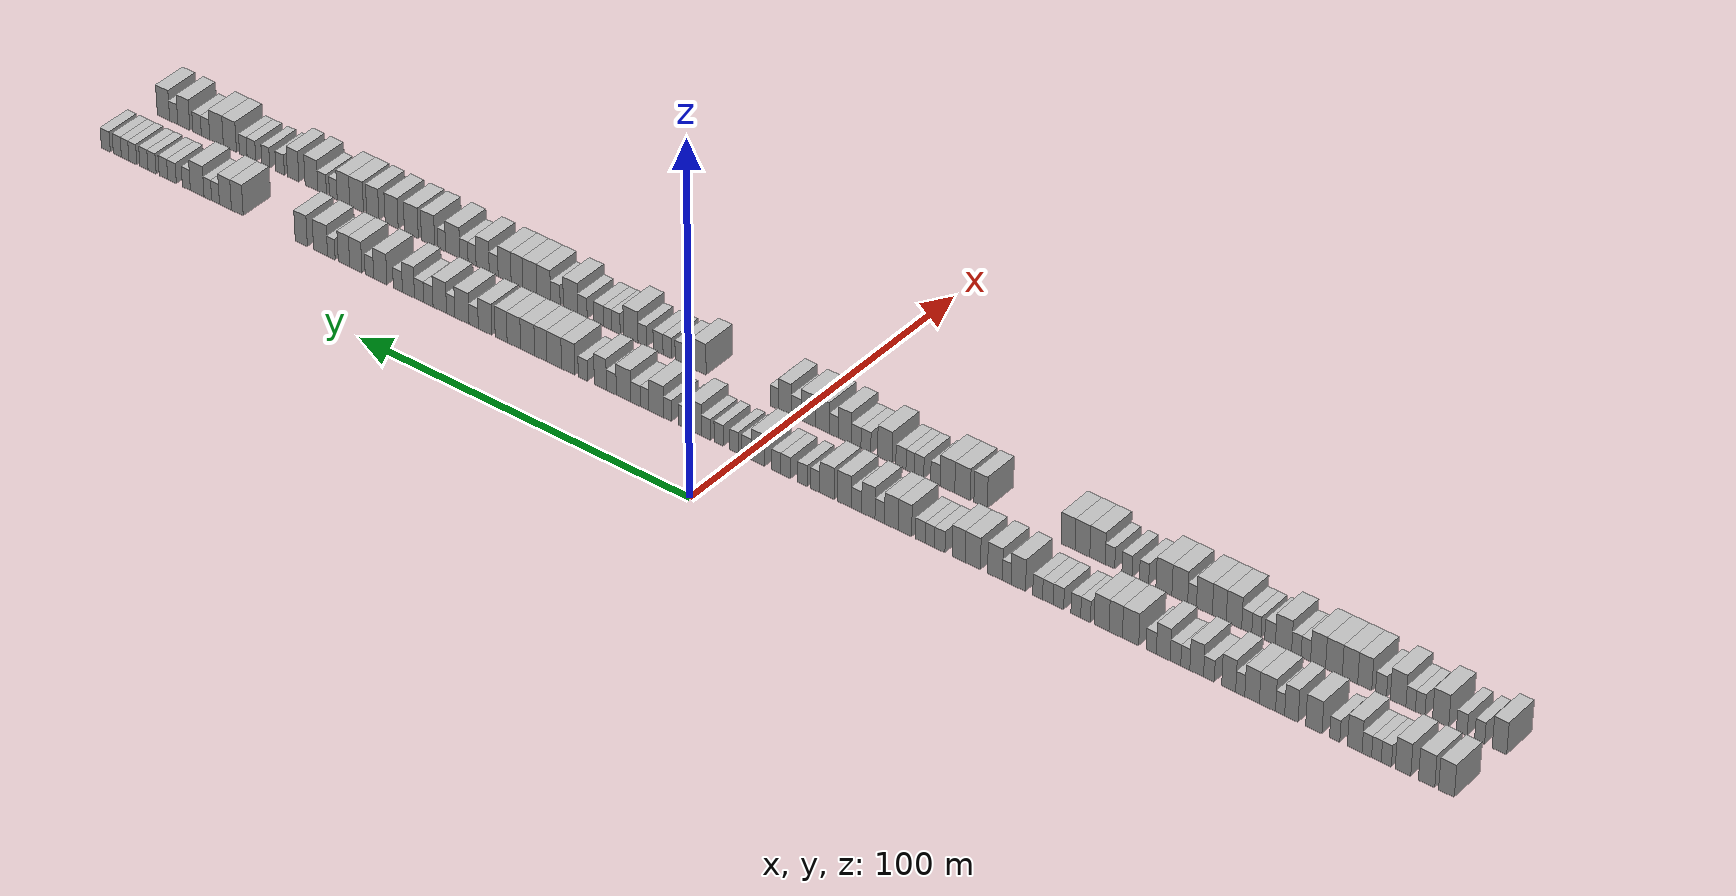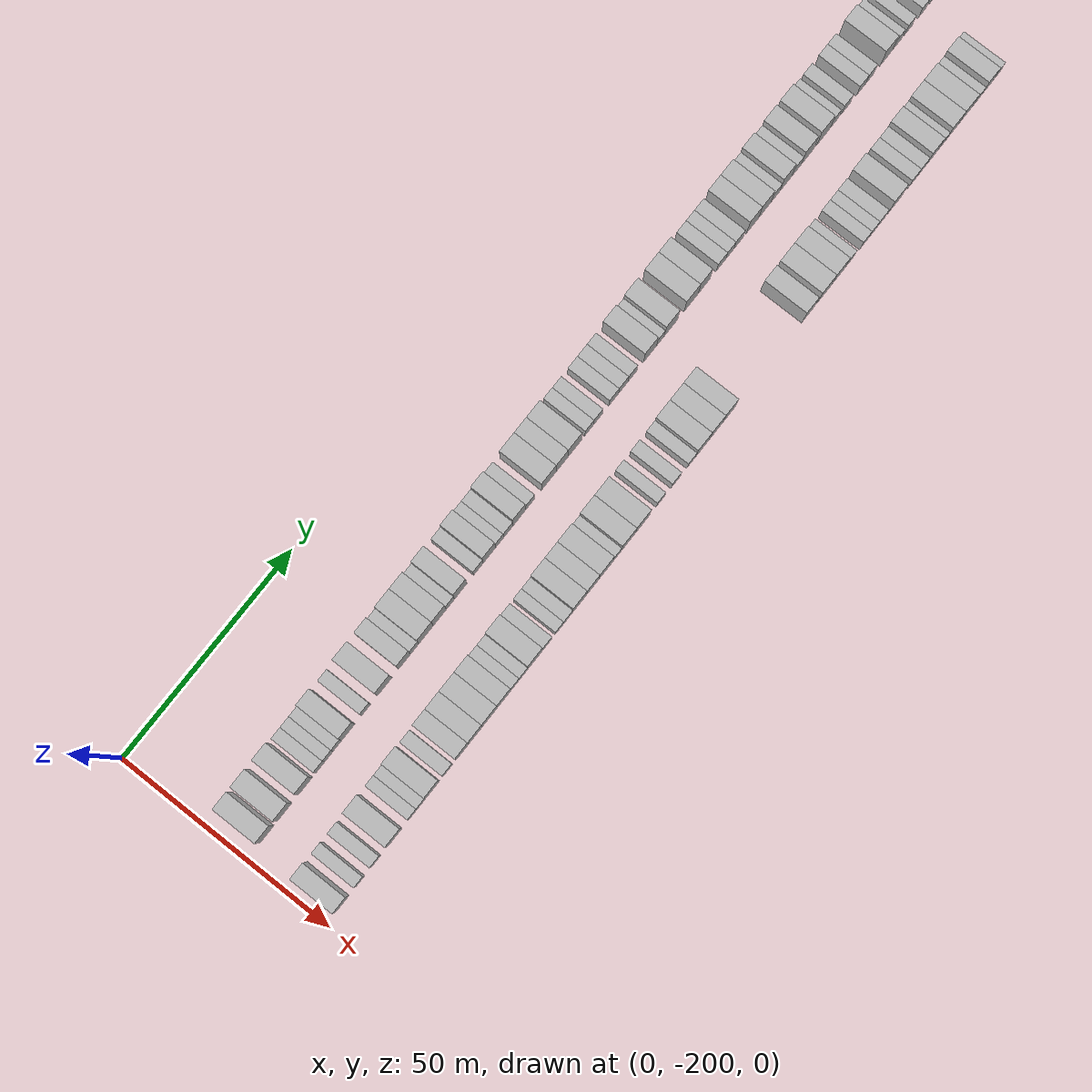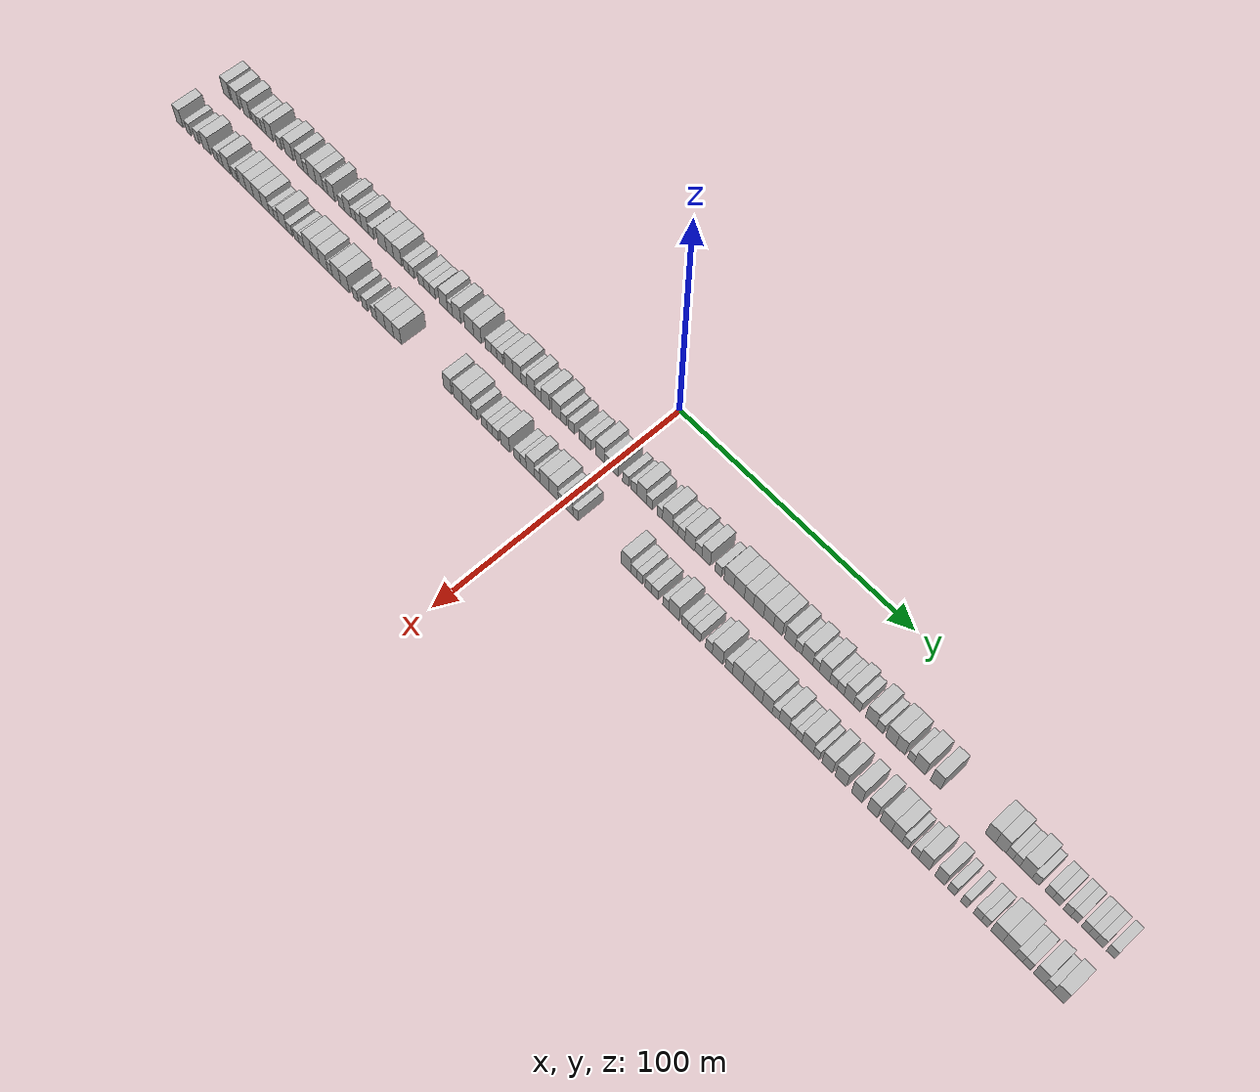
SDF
<sdf version="1.6">
 <world name="default">
  <scene>
   <sky><clouds><speed>12</speed></clouds></sky>
   <ambient>0.4 0.4 0.4 1</ambient>
   <background>0.7 0.7 0.7 1</background>
   <shadows>1</shadows>
  </scene>
  <gravity>0 0 -9.8066</gravity>
  <magnetic_field>6e-06 2.3e-05 -4.2e-05</magnetic_field>
  <physics default="0" name="default_physics" type="ode">
   <ode>
    <solver>
     <type>quick</type>
     <iters>10</iters>
     <sor>1.0</sor>
     <use_dynamic_moi_rescaling>0</use_dynamic_moi_rescaling>
    </solver>
    <constraints>
     <cfm>0</cfm>
     <erp>0.2</erp>
     <contact_max_correcting_vel>100</contact_max_correcting_vel>
     <contact_surface_layer>0.001</contact_surface_layer>
    </constraints>
   </ode>
   <max_step_size>0.004</max_step_size>
   <real_time_factor>1</real_time_factor>
   <real_time_update_rate>250</real_time_update_rate>
  </physics>
  <light name="sun" type="directional">
   <pose>0 0 10 0 0 0</pose>
   <diffuse>0.8 0.8 0.8 1</diffuse>
   <specular>0.2 0.2 0.2 1</specular>
   <attenuation>
    <range>1000</range>
    <constant>0.9</constant>
    <linear>0.01</linear>
    <quadratic>0.001</quadratic>
   </attenuation>
   <direction>-0.5 0.1 -0.9</direction>
  </light>
  <model name="building_1">
   <static>1</static>
   <pose>25.0000 -193.9581 0 0.000000 0.000000 0.000000</pose>
   <link name="link">
    <pose>0 0 4.50 0 0 0</pose>
    <collision name="collision"><geometry><box><size>10.0000 4.0837 9.0000</size></box></geometry></collision>
    <visual name="visual">
     <cast_shadows>0</cast_shadows>
     <geometry><box><size>10.0000 4.0837 9.0000</size></box></geometry>
     <material>
      <script>
       <uri>model://HANNAS_wall/materials/scripts</uri>
       <uri>model://HANNAS_wall/materials/textures</uri>
       <name>vrc/HANNAS_wall</name>
      </script>
     </material>
    </visual>
   </link>
  </model>
  <model name="building_2">
   <static>1</static>
   <pose>25.0000 -188.7889 0 0.000000 0.000000 0.000000</pose>
   <link name="link">
    <pose>0 0 4.50 0 0 0</pose>
    <collision name="collision"><geometry><box><size>10.0000 4.2548 9.0000</size></box></geometry></collision>
    <visual name="visual">
     <cast_shadows>0</cast_shadows>
     <geometry><box><size>10.0000 4.2548 9.0000</size></box></geometry>
     <material>
      <script>
       <uri>model://HANNAS_wall/materials/scripts</uri>
       <uri>model://HANNAS_wall/materials/textures</uri>
       <name>vrc/HANNAS_wall</name>
      </script>
     </material>
    </visual>
   </link>
  </model>
  <model name="building_3">
   <static>1</static>
   <pose>25.0000 -182.6277 0 0.000000 0.000000 0.000000</pose>
   <link name="link">
    <pose>0 0 4.50 0 0 0</pose>
    <collision name="collision"><geometry><box><size>10.0000 4.0676 9.0000</size></box></geometry></collision>
    <visual name="visual">
     <cast_shadows>0</cast_shadows>
     <geometry><box><size>10.0000 4.0676 9.0000</size></box></geometry>
     <material>
      <script>
       <uri>model://HANNAS_wall/materials/scripts</uri>
       <uri>model://HANNAS_wall/materials/textures</uri>
       <name>vrc/HANNAS_wall</name>
      </script>
     </material>
    </visual>
   </link>
  </model>
  <model name="building_4">
   <static>1</static>
   <pose>25.0000 -178.2553 0 0.000000 0.000000 0.000000</pose>
   <link name="link">
    <pose>0 0 3.00 0 0 0</pose>
    <collision name="collision"><geometry><box><size>10.0000 2.6771 6.0000</size></box></geometry></collision>
    <visual name="visual">
     <cast_shadows>0</cast_shadows>
     <geometry><box><size>10.0000 2.6771 6.0000</size></box></geometry>
     <material>
      <script>
       <uri>model://HANNAS_wall/materials/scripts</uri>
       <uri>model://HANNAS_wall/materials/textures</uri>
       <name>vrc/HANNAS_wall</name>
      </script>
     </material>
    </visual>
   </link>
  </model>
  <model name="building_5">
   <static>1</static>
   <pose>25.0000 -175.6578 0 0.000000 0.000000 0.000000</pose>
   <link name="link">
    <pose>0 0 3.00 0 0 0</pose>
    <collision name="collision"><geometry><box><size>10.0000 2.5181 6.0000</size></box></geometry></collision>
    <visual name="visual">
     <cast_shadows>0</cast_shadows>
     <geometry><box><size>10.0000 2.5181 6.0000</size></box></geometry>
     <material>
      <script>
       <uri>model://HANNAS_wall/materials/scripts</uri>
       <uri>model://HANNAS_wall/materials/textures</uri>
       <name>vrc/HANNAS_wall</name>
      </script>
     </material>
    </visual>
   </link>
  </model>
  <model name="building_6">
   <static>1</static>
   <pose>25.0000 -173.1429 0 0.000000 0.000000 0.000000</pose>
   <link name="link">
    <pose>0 0 3.00 0 0 0</pose>
    <collision name="collision"><geometry><box><size>10.0000 2.5117 6.0000</size></box></geometry></collision>
    <visual name="visual">
     <cast_shadows>0</cast_shadows>
     <geometry><box><size>10.0000 2.5117 6.0000</size></box></geometry>
     <material>
      <script>
       <uri>model://HANNAS_wall/materials/scripts</uri>
       <uri>model://HANNAS_wall/materials/textures</uri>
       <name>vrc/HANNAS_wall</name>
      </script>
     </material>
    </visual>
   </link>
  </model>
  <model name="building_7">
   <static>1</static>
   <pose>25.0000 -169.9557 0 0.000000 0.000000 0.000000</pose>
   <link name="link">
    <pose>0 0 4.50 0 0 0</pose>
    <collision name="collision"><geometry><box><size>10.0000 3.8626 9.0000</size></box></geometry></collision>
    <visual name="visual">
     <cast_shadows>0</cast_shadows>
     <geometry><box><size>10.0000 3.8626 9.0000</size></box></geometry>
     <material>
      <script>
       <uri>model://HANNAS_wall/materials/scripts</uri>
       <uri>model://HANNAS_wall/materials/textures</uri>
       <name>vrc/HANNAS_wall</name>
      </script>
     </material>
    </visual>
   </link>
  </model>
  <model name="building_8">
   <static>1</static>
   <pose>25.0000 -164.6663 0 0.000000 0.000000 0.000000</pose>
   <link name="link">
    <pose>0 0 3.00 0 0 0</pose>
    <collision name="collision"><geometry><box><size>10.0000 2.7162 6.0000</size></box></geometry></collision>
    <visual name="visual">
     <cast_shadows>0</cast_shadows>
     <geometry><box><size>10.0000 2.7162 6.0000</size></box></geometry>
     <material>
      <script>
       <uri>model://HANNAS_wall/materials/scripts</uri>
       <uri>model://HANNAS_wall/materials/textures</uri>
       <name>vrc/HANNAS_wall</name>
      </script>
     </material>
    </visual>
   </link>
  </model>
  <model name="building_9">
   <static>1</static>
   <pose>25.0000 -159.1371 0 0.000000 0.000000 0.000000</pose>
   <link name="link">
    <pose>0 0 4.50 0 0 0</pose>
    <collision name="collision"><geometry><box><size>10.0000 4.3422 9.0000</size></box></geometry></collision>
    <visual name="visual">
     <cast_shadows>0</cast_shadows>
     <geometry><box><size>10.0000 4.3422 9.0000</size></box></geometry>
     <material>
      <script>
       <uri>model://HANNAS_wall/materials/scripts</uri>
       <uri>model://HANNAS_wall/materials/textures</uri>
       <name>vrc/HANNAS_wall</name>
      </script>
     </material>
    </visual>
   </link>
  </model>
  <model name="building_10">
   <static>1</static>
   <pose>25.0000 -153.1617 0 0.000000 0.000000 0.000000</pose>
   <link name="link">
    <pose>0 0 4.50 0 0 0</pose>
    <collision name="collision"><geometry><box><size>10.0000 3.6087 9.0000</size></box></geometry></collision>
    <visual name="visual">
     <cast_shadows>0</cast_shadows>
     <geometry><box><size>10.0000 3.6087 9.0000</size></box></geometry>
     <material>
      <script>
       <uri>model://HANNAS_wall/materials/scripts</uri>
       <uri>model://HANNAS_wall/materials/textures</uri>
       <name>vrc/HANNAS_wall</name>
      </script>
     </material>
    </visual>
   </link>
  </model>
  <model name="building_11">
   <static>1</static>
   <pose>25.0000 -150.1485 0 0.000000 0.000000 0.000000</pose>
   <link name="link">
    <pose>0 0 3.00 0 0 0</pose>
    <collision name="collision"><geometry><box><size>10.0000 2.4176 6.0000</size></box></geometry></collision>
    <visual name="visual">
     <cast_shadows>0</cast_shadows>
     <geometry><box><size>10.0000 2.4176 6.0000</size></box></geometry>
     <material>
      <script>
       <uri>model://HANNAS_wall/materials/scripts</uri>
       <uri>model://HANNAS_wall/materials/textures</uri>
       <name>vrc/HANNAS_wall</name>
      </script>
     </material>
    </visual>
   </link>
  </model>
  <model name="building_12">
   <static>1</static>
   <pose>25.0000 -146.7656 0 0.000000 0.000000 0.000000</pose>
   <link name="link">
    <pose>0 0 4.50 0 0 0</pose>
    <collision name="collision"><geometry><box><size>10.0000 4.3481 9.0000</size></box></geometry></collision>
    <visual name="visual">
     <cast_shadows>0</cast_shadows>
     <geometry><box><size>10.0000 4.3481 9.0000</size></box></geometry>
     <material>
      <script>
       <uri>model://HANNAS_wall/materials/scripts</uri>
       <uri>model://HANNAS_wall/materials/textures</uri>
       <name>vrc/HANNAS_wall</name>
      </script>
     </material>
    </visual>
   </link>
  </model>
  <model name="building_13">
   <static>1</static>
   <pose>25.0000 -142.6385 0 0.000000 0.000000 0.000000</pose>
   <link name="link">
    <pose>0 0 4.50 0 0 0</pose>
    <collision name="collision"><geometry><box><size>10.0000 3.9062 9.0000</size></box></geometry></collision>
    <visual name="visual">
     <cast_shadows>0</cast_shadows>
     <geometry><box><size>10.0000 3.9062 9.0000</size></box></geometry>
     <material>
      <script>
       <uri>model://HANNAS_wall/materials/scripts</uri>
       <uri>model://HANNAS_wall/materials/textures</uri>
       <name>vrc/HANNAS_wall</name>
      </script>
     </material>
    </visual>
   </link>
  </model>
  <model name="building_14">
   <static>1</static>
   <pose>25.0000 -139.4596 0 0.000000 0.000000 0.000000</pose>
   <link name="link">
    <pose>0 0 3.00 0 0 0</pose>
    <collision name="collision"><geometry><box><size>10.0000 2.4516 6.0000</size></box></geometry></collision>
    <visual name="visual">
     <cast_shadows>0</cast_shadows>
     <geometry><box><size>10.0000 2.4516 6.0000</size></box></geometry>
     <material>
      <script>
       <uri>model://HANNAS_wall/materials/scripts</uri>
       <uri>model://HANNAS_wall/materials/textures</uri>
       <name>vrc/HANNAS_wall</name>
      </script>
     </material>
    </visual>
   </link>
  </model>
  <model name="building_15">
   <static>1</static>
   <pose>25.0000 -136.3503 0 0.000000 0.000000 0.000000</pose>
   <link name="link">
    <pose>0 0 4.50 0 0 0</pose>
    <collision name="collision"><geometry><box><size>10.0000 3.7671 9.0000</size></box></geometry></collision>
    <visual name="visual">
     <cast_shadows>0</cast_shadows>
     <geometry><box><size>10.0000 3.7671 9.0000</size></box></geometry>
     <material>
      <script>
       <uri>model://HANNAS_wall/materials/scripts</uri>
       <uri>model://HANNAS_wall/materials/textures</uri>
       <name>vrc/HANNAS_wall</name>
      </script>
     </material>
    </visual>
   </link>
  </model>
  <model name="building_16">
   <static>1</static>
   <pose>25.0000 -131.0137 0 0.000000 0.000000 0.000000</pose>
   <link name="link">
    <pose>0 0 3.00 0 0 0</pose>
    <collision name="collision"><geometry><box><size>10.0000 2.9060 6.0000</size></box></geometry></collision>
    <visual name="visual">
     <cast_shadows>0</cast_shadows>
     <geometry><box><size>10.0000 2.9060 6.0000</size></box></geometry>
     <material>
      <script>
       <uri>model://HANNAS_wall/materials/scripts</uri>
       <uri>model://HANNAS_wall/materials/textures</uri>
       <name>vrc/HANNAS_wall</name>
      </script>
     </material>
    </visual>
   </link>
  </model>
  <model name="building_17">
   <static>1</static>
   <pose>25.0000 -127.7043 0 0.000000 0.000000 0.000000</pose>
   <link name="link">
    <pose>0 0 4.50 0 0 0</pose>
    <collision name="collision"><geometry><box><size>10.0000 3.7127 9.0000</size></box></geometry></collision>
    <visual name="visual">
     <cast_shadows>0</cast_shadows>
     <geometry><box><size>10.0000 3.7127 9.0000</size></box></geometry>
     <material>
      <script>
       <uri>model://HANNAS_wall/materials/scripts</uri>
       <uri>model://HANNAS_wall/materials/textures</uri>
       <name>vrc/HANNAS_wall</name>
      </script>
     </material>
    </visual>
   </link>
  </model>
  <model name="building_18">
   <static>1</static>
   <pose>25.0000 -124.6156 0 0.000000 0.000000 0.000000</pose>
   <link name="link">
    <pose>0 0 3.00 0 0 0</pose>
    <collision name="collision"><geometry><box><size>10.0000 2.4646 6.0000</size></box></geometry></collision>
    <visual name="visual">
     <cast_shadows>0</cast_shadows>
     <geometry><box><size>10.0000 2.4646 6.0000</size></box></geometry>
     <material>
      <script>
       <uri>model://HANNAS_wall/materials/scripts</uri>
       <uri>model://HANNAS_wall/materials/textures</uri>
       <name>vrc/HANNAS_wall</name>
      </script>
     </material>
    </visual>
   </link>
  </model>
  <model name="building_19">
   <static>1</static>
   <pose>25.0000 -121.9434 0 0.000000 0.000000 0.000000</pose>
   <link name="link">
    <pose>0 0 3.00 0 0 0</pose>
    <collision name="collision"><geometry><box><size>10.0000 2.8798 6.0000</size></box></geometry></collision>
    <visual name="visual">
     <cast_shadows>0</cast_shadows>
     <geometry><box><size>10.0000 2.8798 6.0000</size></box></geometry>
     <material>
      <script>
       <uri>model://HANNAS_wall/materials/scripts</uri>
       <uri>model://HANNAS_wall/materials/textures</uri>
       <name>vrc/HANNAS_wall</name>
      </script>
     </material>
    </visual>
   </link>
  </model>
  <model name="building_20">
   <static>1</static>
   <pose>25.0000 -118.6147 0 0.000000 0.000000 0.000000</pose>
   <link name="link">
    <pose>0 0 4.50 0 0 0</pose>
    <collision name="collision"><geometry><box><size>10.0000 3.7776 9.0000</size></box></geometry></collision>
    <visual name="visual">
     <cast_shadows>0</cast_shadows>
     <geometry><box><size>10.0000 3.7776 9.0000</size></box></geometry>
     <material>
      <script>
       <uri>model://HANNAS_wall/materials/scripts</uri>
       <uri>model://HANNAS_wall/materials/textures</uri>
       <name>vrc/HANNAS_wall</name>
      </script>
     </material>
    </visual>
   </link>
  </model>
  <model name="building_21">
   <static>1</static>
   <pose>25.0000 -115.3220 0 0.000000 0.000000 0.000000</pose>
   <link name="link">
    <pose>0 0 3.00 0 0 0</pose>
    <collision name="collision"><geometry><box><size>10.0000 2.8077 6.0000</size></box></geometry></collision>
    <visual name="visual">
     <cast_shadows>0</cast_shadows>
     <geometry><box><size>10.0000 2.8077 6.0000</size></box></geometry>
     <material>
      <script>
       <uri>model://HANNAS_wall/materials/scripts</uri>
       <uri>model://HANNAS_wall/materials/textures</uri>
       <name>vrc/HANNAS_wall</name>
      </script>
     </material>
    </visual>
   </link>
  </model>
  <model name="building_22">
   <static>1</static>
   <pose>25.0000 -109.6682 0 0.000000 0.000000 0.000000</pose>
   <link name="link">
    <pose>0 0 4.50 0 0 0</pose>
    <collision name="collision"><geometry><box><size>10.0000 4.4999 9.0000</size></box></geometry></collision>
    <visual name="visual">
     <cast_shadows>0</cast_shadows>
     <geometry><box><size>10.0000 4.4999 9.0000</size></box></geometry>
     <material>
      <script>
       <uri>model://HANNAS_wall/materials/scripts</uri>
       <uri>model://HANNAS_wall/materials/textures</uri>
       <name>vrc/HANNAS_wall</name>
      </script>
     </material>
    </visual>
   </link>
  </model>
  <model name="building_23">
   <static>1</static>
   <pose>25.0000 -105.5826 0 0.000000 0.000000 0.000000</pose>
   <link name="link">
    <pose>0 0 4.50 0 0 0</pose>
    <collision name="collision"><geometry><box><size>10.0000 3.6711 9.0000</size></box></geometry></collision>
    <visual name="visual">
     <cast_shadows>0</cast_shadows>
     <geometry><box><size>10.0000 3.6711 9.0000</size></box></geometry>
     <material>
      <script>
       <uri>model://HANNAS_wall/materials/scripts</uri>
       <uri>model://HANNAS_wall/materials/textures</uri>
       <name>vrc/HANNAS_wall</name>
      </script>
     </material>
    </visual>
   </link>
  </model>
  <model name="building_24">
   <static>1</static>
   <pose>25.0000 -101.6881 0 0.000000 0.000000 0.000000</pose>
   <link name="link">
    <pose>0 0 4.50 0 0 0</pose>
    <collision name="collision"><geometry><box><size>10.0000 4.1179 9.0000</size></box></geometry></collision>
    <visual name="visual">
     <cast_shadows>0</cast_shadows>
     <geometry><box><size>10.0000 4.1179 9.0000</size></box></geometry>
     <material>
      <script>
       <uri>model://HANNAS_wall/materials/scripts</uri>
       <uri>model://HANNAS_wall/materials/textures</uri>
       <name>vrc/HANNAS_wall</name>
      </script>
     </material>
    </visual>
   </link>
  </model>
  <model name="building_25">
   <static>1</static>
   <pose>25.0000 -97.2789 0 0.000000 0.000000 0.000000</pose>
   <link name="link">
    <pose>0 0 3.00 0 0 0</pose>
    <collision name="collision"><geometry><box><size>10.0000 2.7006 6.0000</size></box></geometry></collision>
    <visual name="visual">
     <cast_shadows>0</cast_shadows>
     <geometry><box><size>10.0000 2.7006 6.0000</size></box></geometry>
     <material>
      <script>
       <uri>model://HANNAS_wall/materials/scripts</uri>
       <uri>model://HANNAS_wall/materials/textures</uri>
       <name>vrc/HANNAS_wall</name>
      </script>
     </material>
    </visual>
   </link>
  </model>
  <model name="building_26">
   <static>1</static>
   <pose>25.0000 -94.5722 0 0.000000 0.000000 0.000000</pose>
   <link name="link">
    <pose>0 0 3.00 0 0 0</pose>
    <collision name="collision"><geometry><box><size>10.0000 2.7128 6.0000</size></box></geometry></collision>
    <visual name="visual">
     <cast_shadows>0</cast_shadows>
     <geometry><box><size>10.0000 2.7128 6.0000</size></box></geometry>
     <material>
      <script>
       <uri>model://HANNAS_wall/materials/scripts</uri>
       <uri>model://HANNAS_wall/materials/textures</uri>
       <name>vrc/HANNAS_wall</name>
      </script>
     </material>
    </visual>
   </link>
  </model>
  <model name="building_27">
   <static>1</static>
   <pose>25.0000 -89.7461 0 0.000000 0.000000 0.000000</pose>
   <link name="link">
    <pose>0 0 3.00 0 0 0</pose>
    <collision name="collision"><geometry><box><size>10.0000 2.9394 6.0000</size></box></geometry></collision>
    <visual name="visual">
     <cast_shadows>0</cast_shadows>
     <geometry><box><size>10.0000 2.9394 6.0000</size></box></geometry>
     <material>
      <script>
       <uri>model://HANNAS_wall/materials/scripts</uri>
       <uri>model://HANNAS_wall/materials/textures</uri>
       <name>vrc/HANNAS_wall</name>
      </script>
     </material>
    </visual>
   </link>
  </model>
  <model name="building_28">
   <static>1</static>
   <pose>25.0000 -86.8106 0 0.000000 0.000000 0.000000</pose>
   <link name="link">
    <pose>0 0 3.00 0 0 0</pose>
    <collision name="collision"><geometry><box><size>10.0000 2.9317 6.0000</size></box></geometry></collision>
    <visual name="visual">
     <cast_shadows>0</cast_shadows>
     <geometry><box><size>10.0000 2.9317 6.0000</size></box></geometry>
     <material>
      <script>
       <uri>model://HANNAS_wall/materials/scripts</uri>
       <uri>model://HANNAS_wall/materials/textures</uri>
       <name>vrc/HANNAS_wall</name>
      </script>
     </material>
    </visual>
   </link>
  </model>
  <model name="building_29">
   <static>1</static>
   <pose>25.0000 -83.9705 0 0.000000 0.000000 0.000000</pose>
   <link name="link">
    <pose>0 0 3.00 0 0 0</pose>
    <collision name="collision"><geometry><box><size>10.0000 2.7484 6.0000</size></box></geometry></collision>
    <visual name="visual">
     <cast_shadows>0</cast_shadows>
     <geometry><box><size>10.0000 2.7484 6.0000</size></box></geometry>
     <material>
      <script>
       <uri>model://HANNAS_wall/materials/scripts</uri>
       <uri>model://HANNAS_wall/materials/textures</uri>
       <name>vrc/HANNAS_wall</name>
      </script>
     </material>
    </visual>
   </link>
  </model>
  <model name="building_30">
   <static>1</static>
   <pose>25.0000 -78.5690 0 0.000000 0.000000 0.000000</pose>
   <link name="link">
    <pose>0 0 4.50 0 0 0</pose>
    <collision name="collision"><geometry><box><size>10.0000 4.0546 9.0000</size></box></geometry></collision>
    <visual name="visual">
     <cast_shadows>0</cast_shadows>
     <geometry><box><size>10.0000 4.0546 9.0000</size></box></geometry>
     <material>
      <script>
       <uri>model://HANNAS_wall/materials/scripts</uri>
       <uri>model://HANNAS_wall/materials/textures</uri>
       <name>vrc/HANNAS_wall</name>
      </script>
     </material>
    </visual>
   </link>
  </model>
  <model name="building_31">
   <static>1</static>
   <pose>25.0000 -75.3342 0 0.000000 0.000000 0.000000</pose>
   <link name="link">
    <pose>0 0 3.00 0 0 0</pose>
    <collision name="collision"><geometry><box><size>10.0000 2.4149 6.0000</size></box></geometry></collision>
    <visual name="visual">
     <cast_shadows>0</cast_shadows>
     <geometry><box><size>10.0000 2.4149 6.0000</size></box></geometry>
     <material>
      <script>
       <uri>model://HANNAS_wall/materials/scripts</uri>
       <uri>model://HANNAS_wall/materials/textures</uri>
       <name>vrc/HANNAS_wall</name>
      </script>
     </material>
    </visual>
   </link>
  </model>
  <model name="building_32">
   <static>1</static>
   <pose>25.0000 -72.0276 0 0.000000 0.000000 0.000000</pose>
   <link name="link">
    <pose>0 0 4.50 0 0 0</pose>
    <collision name="collision"><geometry><box><size>10.0000 4.1984 9.0000</size></box></geometry></collision>
    <visual name="visual">
     <cast_shadows>0</cast_shadows>
     <geometry><box><size>10.0000 4.1984 9.0000</size></box></geometry>
     <material>
      <script>
       <uri>model://HANNAS_wall/materials/scripts</uri>
       <uri>model://HANNAS_wall/materials/textures</uri>
       <name>vrc/HANNAS_wall</name>
      </script>
     </material>
    </visual>
   </link>
  </model>
  <model name="building_33">
   <static>1</static>
   <pose>25.0000 -65.7691 0 0.000000 0.000000 0.000000</pose>
   <link name="link">
    <pose>0 0 4.50 0 0 0</pose>
    <collision name="collision"><geometry><box><size>10.0000 4.3185 9.0000</size></box></geometry></collision>
    <visual name="visual">
     <cast_shadows>0</cast_shadows>
     <geometry><box><size>10.0000 4.3185 9.0000</size></box></geometry>
     <material>
      <script>
       <uri>model://HANNAS_wall/materials/scripts</uri>
       <uri>model://HANNAS_wall/materials/textures</uri>
       <name>vrc/HANNAS_wall</name>
      </script>
     </material>
    </visual>
   </link>
  </model>
  <model name="building_34">
   <static>1</static>
   <pose>25.0000 -61.7479 0 0.000000 0.000000 0.000000</pose>
   <link name="link">
    <pose>0 0 4.50 0 0 0</pose>
    <collision name="collision"><geometry><box><size>10.0000 3.7239 9.0000</size></box></geometry></collision>
    <visual name="visual">
     <cast_shadows>0</cast_shadows>
     <geometry><box><size>10.0000 3.7239 9.0000</size></box></geometry>
     <material>
      <script>
       <uri>model://HANNAS_wall/materials/scripts</uri>
       <uri>model://HANNAS_wall/materials/textures</uri>
       <name>vrc/HANNAS_wall</name>
      </script>
     </material>
    </visual>
   </link>
  </model>
  <model name="building_35">
   <static>1</static>
   <pose>25.0000 -56.4056 0 0.000000 0.000000 0.000000</pose>
   <link name="link">
    <pose>0 0 3.00 0 0 0</pose>
    <collision name="collision"><geometry><box><size>10.0000 2.9605 6.0000</size></box></geometry></collision>
    <visual name="visual">
     <cast_shadows>0</cast_shadows>
     <geometry><box><size>10.0000 2.9605 6.0000</size></box></geometry>
     <material>
      <script>
       <uri>model://HANNAS_wall/materials/scripts</uri>
       <uri>model://HANNAS_wall/materials/textures</uri>
       <name>vrc/HANNAS_wall</name>
      </script>
     </material>
    </visual>
   </link>
  </model>
  <model name="building_36">
   <static>1</static>
   <pose>25.0000 -53.6233 0 0.000000 0.000000 0.000000</pose>
   <link name="link">
    <pose>0 0 3.00 0 0 0</pose>
    <collision name="collision"><geometry><box><size>10.0000 2.6041 6.0000</size></box></geometry></collision>
    <visual name="visual">
     <cast_shadows>0</cast_shadows>
     <geometry><box><size>10.0000 2.6041 6.0000</size></box></geometry>
     <material>
      <script>
       <uri>model://HANNAS_wall/materials/scripts</uri>
       <uri>model://HANNAS_wall/materials/textures</uri>
       <name>vrc/HANNAS_wall</name>
      </script>
     </material>
    </visual>
   </link>
  </model>
  <model name="building_37">
   <static>1</static>
   <pose>25.0000 -50.8717 0 0.000000 0.000000 0.000000</pose>
   <link name="link">
    <pose>0 0 3.00 0 0 0</pose>
    <collision name="collision"><geometry><box><size>10.0000 2.8991 6.0000</size></box></geometry></collision>
    <visual name="visual">
     <cast_shadows>0</cast_shadows>
     <geometry><box><size>10.0000 2.8991 6.0000</size></box></geometry>
     <material>
      <script>
       <uri>model://HANNAS_wall/materials/scripts</uri>
       <uri>model://HANNAS_wall/materials/textures</uri>
       <name>vrc/HANNAS_wall</name>
      </script>
     </material>
    </visual>
   </link>
  </model>
  <model name="building_38">
   <static>1</static>
   <pose>25.0000 -46.5042 0 0.000000 0.000000 0.000000</pose>
   <link name="link">
    <pose>0 0 4.50 0 0 0</pose>
    <collision name="collision"><geometry><box><size>10.0000 3.8361 9.0000</size></box></geometry></collision>
    <visual name="visual">
     <cast_shadows>0</cast_shadows>
     <geometry><box><size>10.0000 3.8361 9.0000</size></box></geometry>
     <material>
      <script>
       <uri>model://HANNAS_wall/materials/scripts</uri>
       <uri>model://HANNAS_wall/materials/textures</uri>
       <name>vrc/HANNAS_wall</name>
      </script>
     </material>
    </visual>
   </link>
  </model>
  <model name="building_39">
   <static>1</static>
   <pose>25.0000 -42.6368 0 0.000000 0.000000 0.000000</pose>
   <link name="link">
    <pose>0 0 4.50 0 0 0</pose>
    <collision name="collision"><geometry><box><size>10.0000 3.8986 9.0000</size></box></geometry></collision>
    <visual name="visual">
     <cast_shadows>0</cast_shadows>
     <geometry><box><size>10.0000 3.8986 9.0000</size></box></geometry>
     <material>
      <script>
       <uri>model://HANNAS_wall/materials/scripts</uri>
       <uri>model://HANNAS_wall/materials/textures</uri>
       <name>vrc/HANNAS_wall</name>
      </script>
     </material>
    </visual>
   </link>
  </model>
  <model name="building_40">
   <static>1</static>
   <pose>25.0000 -39.2942 0 0.000000 0.000000 0.000000</pose>
   <link name="link">
    <pose>0 0 3.00 0 0 0</pose>
    <collision name="collision"><geometry><box><size>10.0000 2.7866 6.0000</size></box></geometry></collision>
    <visual name="visual">
     <cast_shadows>0</cast_shadows>
     <geometry><box><size>10.0000 2.7866 6.0000</size></box></geometry>
     <material>
      <script>
       <uri>model://HANNAS_wall/materials/scripts</uri>
       <uri>model://HANNAS_wall/materials/textures</uri>
       <name>vrc/HANNAS_wall</name>
      </script>
     </material>
    </visual>
   </link>
  </model>
  <model name="building_41">
   <static>1</static>
   <pose>25.0000 -36.0034 0 0.000000 0.000000 0.000000</pose>
   <link name="link">
    <pose>0 0 4.50 0 0 0</pose>
    <collision name="collision"><geometry><box><size>10.0000 3.7951 9.0000</size></box></geometry></collision>
    <visual name="visual">
     <cast_shadows>0</cast_shadows>
     <geometry><box><size>10.0000 3.7951 9.0000</size></box></geometry>
     <material>
      <script>
       <uri>model://HANNAS_wall/materials/scripts</uri>
       <uri>model://HANNAS_wall/materials/textures</uri>
       <name>vrc/HANNAS_wall</name>
      </script>
     </material>
    </visual>
   </link>
  </model>
  <model name="building_42">
   <static>1</static>
   <pose>25.0000 -32.6270 0 0.000000 0.000000 0.000000</pose>
   <link name="link">
    <pose>0 0 3.00 0 0 0</pose>
    <collision name="collision"><geometry><box><size>10.0000 2.9575 6.0000</size></box></geometry></collision>
    <visual name="visual">
     <cast_shadows>0</cast_shadows>
     <geometry><box><size>10.0000 2.9575 6.0000</size></box></geometry>
     <material>
      <script>
       <uri>model://HANNAS_wall/materials/scripts</uri>
       <uri>model://HANNAS_wall/materials/textures</uri>
       <name>vrc/HANNAS_wall</name>
      </script>
     </material>
    </visual>
   </link>
  </model>
  <model name="building_43">
   <static>1</static>
   <pose>25.0000 -29.1503 0 0.000000 0.000000 0.000000</pose>
   <link name="link">
    <pose>0 0 4.50 0 0 0</pose>
    <collision name="collision"><geometry><box><size>10.0000 3.9960 9.0000</size></box></geometry></collision>
    <visual name="visual">
     <cast_shadows>0</cast_shadows>
     <geometry><box><size>10.0000 3.9960 9.0000</size></box></geometry>
     <material>
      <script>
       <uri>model://HANNAS_wall/materials/scripts</uri>
       <uri>model://HANNAS_wall/materials/textures</uri>
       <name>vrc/HANNAS_wall</name>
      </script>
     </material>
    </visual>
   </link>
  </model>
  <model name="building_44">
   <static>1</static>
   <pose>25.0000 -24.0661 0 0.000000 0.000000 0.000000</pose>
   <link name="link">
    <pose>0 0 4.50 0 0 0</pose>
    <collision name="collision"><geometry><box><size>10.0000 4.1723 9.0000</size></box></geometry></collision>
    <visual name="visual">
     <cast_shadows>0</cast_shadows>
     <geometry><box><size>10.0000 4.1723 9.0000</size></box></geometry>
     <material>
      <script>
       <uri>model://HANNAS_wall/materials/scripts</uri>
       <uri>model://HANNAS_wall/materials/textures</uri>
       <name>vrc/HANNAS_wall</name>
      </script>
     </material>
    </visual>
   </link>
  </model>
  <model name="building_45">
   <static>1</static>
   <pose>25.0000 -20.6764 0 0.000000 0.000000 0.000000</pose>
   <link name="link">
    <pose>0 0 3.00 0 0 0</pose>
    <collision name="collision"><geometry><box><size>10.0000 2.6072 6.0000</size></box></geometry></collision>
    <visual name="visual">
     <cast_shadows>0</cast_shadows>
     <geometry><box><size>10.0000 2.6072 6.0000</size></box></geometry>
     <material>
      <script>
       <uri>model://HANNAS_wall/materials/scripts</uri>
       <uri>model://HANNAS_wall/materials/textures</uri>
       <name>vrc/HANNAS_wall</name>
      </script>
     </material>
    </visual>
   </link>
  </model>
  <model name="building_46">
   <static>1</static>
   <pose>25.0000 -16.9450 0 0.000000 0.000000 0.000000</pose>
   <link name="link">
    <pose>0 0 3.00 0 0 0</pose>
    <collision name="collision"><geometry><box><size>10.0000 2.8556 6.0000</size></box></geometry></collision>
    <visual name="visual">
     <cast_shadows>0</cast_shadows>
     <geometry><box><size>10.0000 2.8556 6.0000</size></box></geometry>
     <material>
      <script>
       <uri>model://HANNAS_wall/materials/scripts</uri>
       <uri>model://HANNAS_wall/materials/textures</uri>
       <name>vrc/HANNAS_wall</name>
      </script>
     </material>
    </visual>
   </link>
  </model>
  <model name="building_47">
   <static>1</static>
   <pose>25.0000 -12.0820 0 0.000000 0.000000 0.000000</pose>
   <link name="link">
    <pose>0 0 3.00 0 0 0</pose>
    <collision name="collision"><geometry><box><size>10.0000 2.8704 6.0000</size></box></geometry></collision>
    <visual name="visual">
     <cast_shadows>0</cast_shadows>
     <geometry><box><size>10.0000 2.8704 6.0000</size></box></geometry>
     <material>
      <script>
       <uri>model://HANNAS_wall/materials/scripts</uri>
       <uri>model://HANNAS_wall/materials/textures</uri>
       <name>vrc/HANNAS_wall</name>
      </script>
     </material>
    </visual>
   </link>
  </model>
  <model name="building_48">
   <static>1</static>
   <pose>25.0000 -9.2981 0 0.000000 0.000000 0.000000</pose>
   <link name="link">
    <pose>0 0 3.00 0 0 0</pose>
    <collision name="collision"><geometry><box><size>10.0000 2.6974 6.0000</size></box></geometry></collision>
    <visual name="visual">
     <cast_shadows>0</cast_shadows>
     <geometry><box><size>10.0000 2.6974 6.0000</size></box></geometry>
     <material>
      <script>
       <uri>model://HANNAS_wall/materials/scripts</uri>
       <uri>model://HANNAS_wall/materials/textures</uri>
       <name>vrc/HANNAS_wall</name>
      </script>
     </material>
    </visual>
   </link>
  </model>
  <model name="building_49">
   <static>1</static>
   <pose>25.0000 -3.9427 0 0.000000 0.000000 0.000000</pose>
   <link name="link">
    <pose>0 0 4.50 0 0 0</pose>
    <collision name="collision"><geometry><box><size>10.0000 4.0133 9.0000</size></box></geometry></collision>
    <visual name="visual">
     <cast_shadows>0</cast_shadows>
     <geometry><box><size>10.0000 4.0133 9.0000</size></box></geometry>
     <material>
      <script>
       <uri>model://HANNAS_wall/materials/scripts</uri>
       <uri>model://HANNAS_wall/materials/textures</uri>
       <name>vrc/HANNAS_wall</name>
      </script>
     </material>
    </visual>
   </link>
  </model>
  <model name="building_50">
   <static>1</static>
   <pose>25.0000 -0.5174 0 0.000000 0.000000 0.000000</pose>
   <link name="link">
    <pose>0 0 3.00 0 0 0</pose>
    <collision name="collision"><geometry><box><size>10.0000 2.8372 6.0000</size></box></geometry></collision>
    <visual name="visual">
     <cast_shadows>0</cast_shadows>
     <geometry><box><size>10.0000 2.8372 6.0000</size></box></geometry>
     <material>
      <script>
       <uri>model://HANNAS_wall/materials/scripts</uri>
       <uri>model://HANNAS_wall/materials/textures</uri>
       <name>vrc/HANNAS_wall</name>
      </script>
     </material>
    </visual>
   </link>
  </model>
  <model name="building_51">
   <static>1</static>
   <pose>25.0000 3.1244 0 0.000000 0.000000 0.000000</pose>
   <link name="link">
    <pose>0 0 3.00 0 0 0</pose>
    <collision name="collision"><geometry><box><size>10.0000 2.4465 6.0000</size></box></geometry></collision>
    <visual name="visual">
     <cast_shadows>0</cast_shadows>
     <geometry><box><size>10.0000 2.4465 6.0000</size></box></geometry>
     <material>
      <script>
       <uri>model://HANNAS_wall/materials/scripts</uri>
       <uri>model://HANNAS_wall/materials/textures</uri>
       <name>vrc/HANNAS_wall</name>
      </script>
     </material>
    </visual>
   </link>
  </model>
  <model name="building_52">
   <static>1</static>
   <pose>25.0000 7.6883 0 0.000000 0.000000 0.000000</pose>
   <link name="link">
    <pose>0 0 3.00 0 0 0</pose>
    <collision name="collision"><geometry><box><size>10.0000 2.6811 6.0000</size></box></geometry></collision>
    <visual name="visual">
     <cast_shadows>0</cast_shadows>
     <geometry><box><size>10.0000 2.6811 6.0000</size></box></geometry>
     <material>
      <script>
       <uri>model://HANNAS_wall/materials/scripts</uri>
       <uri>model://HANNAS_wall/materials/textures</uri>
       <name>vrc/HANNAS_wall</name>
      </script>
     </material>
    </visual>
   </link>
  </model>
  <model name="building_53">
   <static>1</static>
   <pose>25.0000 11.4147 0 0.000000 0.000000 0.000000</pose>
   <link name="link">
    <pose>0 0 3.00 0 0 0</pose>
    <collision name="collision"><geometry><box><size>10.0000 2.7717 6.0000</size></box></geometry></collision>
    <visual name="visual">
     <cast_shadows>0</cast_shadows>
     <geometry><box><size>10.0000 2.7717 6.0000</size></box></geometry>
     <material>
      <script>
       <uri>model://HANNAS_wall/materials/scripts</uri>
       <uri>model://HANNAS_wall/materials/textures</uri>
       <name>vrc/HANNAS_wall</name>
      </script>
     </material>
    </visual>
   </link>
  </model>
  <model name="building_54">
   <static>1</static>
   <pose>25.0000 14.8479 0 0.000000 0.000000 0.000000</pose>
   <link name="link">
    <pose>0 0 4.50 0 0 0</pose>
    <collision name="collision"><geometry><box><size>10.0000 4.0949 9.0000</size></box></geometry></collision>
    <visual name="visual">
     <cast_shadows>0</cast_shadows>
     <geometry><box><size>10.0000 4.0949 9.0000</size></box></geometry>
     <material>
      <script>
       <uri>model://HANNAS_wall/materials/scripts</uri>
       <uri>model://HANNAS_wall/materials/textures</uri>
       <name>vrc/HANNAS_wall</name>
      </script>
     </material>
    </visual>
   </link>
  </model>
  <model name="building_55">
   <static>1</static>
   <pose>25.0000 18.2816 0 0.000000 0.000000 0.000000</pose>
   <link name="link">
    <pose>0 0 3.00 0 0 0</pose>
    <collision name="collision"><geometry><box><size>10.0000 2.7725 6.0000</size></box></geometry></collision>
    <visual name="visual">
     <cast_shadows>0</cast_shadows>
     <geometry><box><size>10.0000 2.7725 6.0000</size></box></geometry>
     <material>
      <script>
       <uri>model://HANNAS_wall/materials/scripts</uri>
       <uri>model://HANNAS_wall/materials/textures</uri>
       <name>vrc/HANNAS_wall</name>
      </script>
     </material>
    </visual>
   </link>
  </model>
  <model name="building_56">
   <static>1</static>
   <pose>25.0000 22.8732 0 0.000000 0.000000 0.000000</pose>
   <link name="link">
    <pose>0 0 3.00 0 0 0</pose>
    <collision name="collision"><geometry><box><size>10.0000 2.4108 6.0000</size></box></geometry></collision>
    <visual name="visual">
     <cast_shadows>0</cast_shadows>
     <geometry><box><size>10.0000 2.4108 6.0000</size></box></geometry>
     <material>
      <script>
       <uri>model://HANNAS_wall/materials/scripts</uri>
       <uri>model://HANNAS_wall/materials/textures</uri>
       <name>vrc/HANNAS_wall</name>
      </script>
     </material>
    </visual>
   </link>
  </model>
  <model name="building_57">
   <static>1</static>
   <pose>25.0000 26.2850 0 0.000000 0.000000 0.000000</pose>
   <link name="link">
    <pose>0 0 4.50 0 0 0</pose>
    <collision name="collision"><geometry><box><size>10.0000 4.4127 9.0000</size></box></geometry></collision>
    <visual name="visual">
     <cast_shadows>0</cast_shadows>
     <geometry><box><size>10.0000 4.4127 9.0000</size></box></geometry>
     <material>
      <script>
       <uri>model://HANNAS_wall/materials/scripts</uri>
       <uri>model://HANNAS_wall/materials/textures</uri>
       <name>vrc/HANNAS_wall</name>
      </script>
     </material>
    </visual>
   </link>
  </model>
  <model name="building_58">
   <static>1</static>
   <pose>25.0000 29.7248 0 0.000000 0.000000 0.000000</pose>
   <link name="link">
    <pose>0 0 3.00 0 0 0</pose>
    <collision name="collision"><geometry><box><size>10.0000 2.4670 6.0000</size></box></geometry></collision>
    <visual name="visual">
     <cast_shadows>0</cast_shadows>
     <geometry><box><size>10.0000 2.4670 6.0000</size></box></geometry>
     <material>
      <script>
       <uri>model://HANNAS_wall/materials/scripts</uri>
       <uri>model://HANNAS_wall/materials/textures</uri>
       <name>vrc/HANNAS_wall</name>
      </script>
     </material>
    </visual>
   </link>
  </model>
  <model name="building_59">
   <static>1</static>
   <pose>25.0000 32.4260 0 0.000000 0.000000 0.000000</pose>
   <link name="link">
    <pose>0 0 3.00 0 0 0</pose>
    <collision name="collision"><geometry><box><size>10.0000 2.9354 6.0000</size></box></geometry></collision>
    <visual name="visual">
     <cast_shadows>0</cast_shadows>
     <geometry><box><size>10.0000 2.9354 6.0000</size></box></geometry>
     <material>
      <script>
       <uri>model://HANNAS_wall/materials/scripts</uri>
       <uri>model://HANNAS_wall/materials/textures</uri>
       <name>vrc/HANNAS_wall</name>
      </script>
     </material>
    </visual>
   </link>
  </model>
  <model name="building_60">
   <static>1</static>
   <pose>25.0000 36.0770 0 0.000000 0.000000 0.000000</pose>
   <link name="link">
    <pose>0 0 4.50 0 0 0</pose>
    <collision name="collision"><geometry><box><size>10.0000 4.3665 9.0000</size></box></geometry></collision>
    <visual name="visual">
     <cast_shadows>0</cast_shadows>
     <geometry><box><size>10.0000 4.3665 9.0000</size></box></geometry>
     <material>
      <script>
       <uri>model://HANNAS_wall/materials/scripts</uri>
       <uri>model://HANNAS_wall/materials/textures</uri>
       <name>vrc/HANNAS_wall</name>
      </script>
     </material>
    </visual>
   </link>
  </model>
  <model name="building_61">
   <static>1</static>
   <pose>25.0000 39.7541 0 0.000000 0.000000 0.000000</pose>
   <link name="link">
    <pose>0 0 3.00 0 0 0</pose>
    <collision name="collision"><geometry><box><size>10.0000 2.9877 6.0000</size></box></geometry></collision>
    <visual name="visual">
     <cast_shadows>0</cast_shadows>
     <geometry><box><size>10.0000 2.9877 6.0000</size></box></geometry>
     <material>
      <script>
       <uri>model://HANNAS_wall/materials/scripts</uri>
       <uri>model://HANNAS_wall/materials/textures</uri>
       <name>vrc/HANNAS_wall</name>
      </script>
     </material>
    </visual>
   </link>
  </model>
  <model name="building_62">
   <static>1</static>
   <pose>25.0000 43.0834 0 0.000000 0.000000 0.000000</pose>
   <link name="link">
    <pose>0 0 4.50 0 0 0</pose>
    <collision name="collision"><geometry><box><size>10.0000 3.6708 9.0000</size></box></geometry></collision>
    <visual name="visual">
     <cast_shadows>0</cast_shadows>
     <geometry><box><size>10.0000 3.6708 9.0000</size></box></geometry>
     <material>
      <script>
       <uri>model://HANNAS_wall/materials/scripts</uri>
       <uri>model://HANNAS_wall/materials/textures</uri>
       <name>vrc/HANNAS_wall</name>
      </script>
     </material>
    </visual>
   </link>
  </model>
  <model name="building_63">
   <static>1</static>
   <pose>25.0000 48.3474 0 0.000000 0.000000 0.000000</pose>
   <link name="link">
    <pose>0 0 3.00 0 0 0</pose>
    <collision name="collision"><geometry><box><size>10.0000 2.8573 6.0000</size></box></geometry></collision>
    <visual name="visual">
     <cast_shadows>0</cast_shadows>
     <geometry><box><size>10.0000 2.8573 6.0000</size></box></geometry>
     <material>
      <script>
       <uri>model://HANNAS_wall/materials/scripts</uri>
       <uri>model://HANNAS_wall/materials/textures</uri>
       <name>vrc/HANNAS_wall</name>
      </script>
     </material>
    </visual>
   </link>
  </model>
  <model name="building_64">
   <static>1</static>
   <pose>25.0000 52.8210 0 0.000000 0.000000 0.000000</pose>
   <link name="link">
    <pose>0 0 4.50 0 0 0</pose>
    <collision name="collision"><geometry><box><size>10.0000 4.0899 9.0000</size></box></geometry></collision>
    <visual name="visual">
     <cast_shadows>0</cast_shadows>
     <geometry><box><size>10.0000 4.0899 9.0000</size></box></geometry>
     <material>
      <script>
       <uri>model://HANNAS_wall/materials/scripts</uri>
       <uri>model://HANNAS_wall/materials/textures</uri>
       <name>vrc/HANNAS_wall</name>
      </script>
     </material>
    </visual>
   </link>
  </model>
  <model name="building_65">
   <static>1</static>
   <pose>25.0000 57.0974 0 0.000000 0.000000 0.000000</pose>
   <link name="link">
    <pose>0 0 4.50 0 0 0</pose>
    <collision name="collision"><geometry><box><size>10.0000 4.4629 9.0000</size></box></geometry></collision>
    <visual name="visual">
     <cast_shadows>0</cast_shadows>
     <geometry><box><size>10.0000 4.4629 9.0000</size></box></geometry>
     <material>
      <script>
       <uri>model://HANNAS_wall/materials/scripts</uri>
       <uri>model://HANNAS_wall/materials/textures</uri>
       <name>vrc/HANNAS_wall</name>
      </script>
     </material>
    </visual>
   </link>
  </model>
  <model name="building_66">
   <static>1</static>
   <pose>25.0000 61.1951 0 0.000000 0.000000 0.000000</pose>
   <link name="link">
    <pose>0 0 4.50 0 0 0</pose>
    <collision name="collision"><geometry><box><size>10.0000 3.7323 9.0000</size></box></geometry></collision>
    <visual name="visual">
     <cast_shadows>0</cast_shadows>
     <geometry><box><size>10.0000 3.7323 9.0000</size></box></geometry>
     <material>
      <script>
       <uri>model://HANNAS_wall/materials/scripts</uri>
       <uri>model://HANNAS_wall/materials/textures</uri>
       <name>vrc/HANNAS_wall</name>
      </script>
     </material>
    </visual>
   </link>
  </model>
  <model name="building_67">
   <static>1</static>
   <pose>25.0000 65.2135 0 0.000000 0.000000 0.000000</pose>
   <link name="link">
    <pose>0 0 4.50 0 0 0</pose>
    <collision name="collision"><geometry><box><size>10.0000 4.3045 9.0000</size></box></geometry></collision>
    <visual name="visual">
     <cast_shadows>0</cast_shadows>
     <geometry><box><size>10.0000 4.3045 9.0000</size></box></geometry>
     <material>
      <script>
       <uri>model://HANNAS_wall/materials/scripts</uri>
       <uri>model://HANNAS_wall/materials/textures</uri>
       <name>vrc/HANNAS_wall</name>
      </script>
     </material>
    </visual>
   </link>
  </model>
  <model name="building_68">
   <static>1</static>
   <pose>25.0000 69.4503 0 0.000000 0.000000 0.000000</pose>
   <link name="link">
    <pose>0 0 4.50 0 0 0</pose>
    <collision name="collision"><geometry><box><size>10.0000 4.1691 9.0000</size></box></geometry></collision>
    <visual name="visual">
     <cast_shadows>0</cast_shadows>
     <geometry><box><size>10.0000 4.1691 9.0000</size></box></geometry>
     <material>
      <script>
       <uri>model://HANNAS_wall/materials/scripts</uri>
       <uri>model://HANNAS_wall/materials/textures</uri>
       <name>vrc/HANNAS_wall</name>
      </script>
     </material>
    </visual>
   </link>
  </model>
  <model name="building_69">
   <static>1</static>
   <pose>25.0000 73.3714 0 0.000000 0.000000 0.000000</pose>
   <link name="link">
    <pose>0 0 4.50 0 0 0</pose>
    <collision name="collision"><geometry><box><size>10.0000 3.6731 9.0000</size></box></geometry></collision>
    <visual name="visual">
     <cast_shadows>0</cast_shadows>
     <geometry><box><size>10.0000 3.6731 9.0000</size></box></geometry>
     <material>
      <script>
       <uri>model://HANNAS_wall/materials/scripts</uri>
       <uri>model://HANNAS_wall/materials/textures</uri>
       <name>vrc/HANNAS_wall</name>
      </script>
     </material>
    </visual>
   </link>
  </model>
  <model name="building_70">
   <static>1</static>
   <pose>25.0000 78.3073 0 0.000000 0.000000 0.000000</pose>
   <link name="link">
    <pose>0 0 4.50 0 0 0</pose>
    <collision name="collision"><geometry><box><size>10.0000 4.1988 9.0000</size></box></geometry></collision>
    <visual name="visual">
     <cast_shadows>0</cast_shadows>
     <geometry><box><size>10.0000 4.1988 9.0000</size></box></geometry>
     <material>
      <script>
       <uri>model://HANNAS_wall/materials/scripts</uri>
       <uri>model://HANNAS_wall/materials/textures</uri>
       <name>vrc/HANNAS_wall</name>
      </script>
     </material>
    </visual>
   </link>
  </model>
  <model name="building_71">
   <static>1</static>
   <pose>25.0000 81.8561 0 0.000000 0.000000 0.000000</pose>
   <link name="link">
    <pose>0 0 3.00 0 0 0</pose>
    <collision name="collision"><geometry><box><size>10.0000 2.8987 6.0000</size></box></geometry></collision>
    <visual name="visual">
     <cast_shadows>0</cast_shadows>
     <geometry><box><size>10.0000 2.8987 6.0000</size></box></geometry>
     <material>
      <script>
       <uri>model://HANNAS_wall/materials/scripts</uri>
       <uri>model://HANNAS_wall/materials/textures</uri>
       <name>vrc/HANNAS_wall</name>
      </script>
     </material>
    </visual>
   </link>
  </model>
  <model name="building_72">
   <static>1</static>
   <pose>25.0000 85.4938 0 0.000000 0.000000 0.000000</pose>
   <link name="link">
    <pose>0 0 4.50 0 0 0</pose>
    <collision name="collision"><geometry><box><size>10.0000 4.3767 9.0000</size></box></geometry></collision>
    <visual name="visual">
     <cast_shadows>0</cast_shadows>
     <geometry><box><size>10.0000 4.3767 9.0000</size></box></geometry>
     <material>
      <script>
       <uri>model://HANNAS_wall/materials/scripts</uri>
       <uri>model://HANNAS_wall/materials/textures</uri>
       <name>vrc/HANNAS_wall</name>
      </script>
     </material>
    </visual>
   </link>
  </model>
  <model name="building_73">
   <static>1</static>
   <pose>25.0000 88.9844 0 0.000000 0.000000 0.000000</pose>
   <link name="link">
    <pose>0 0 3.00 0 0 0</pose>
    <collision name="collision"><geometry><box><size>10.0000 2.6045 6.0000</size></box></geometry></collision>
    <visual name="visual">
     <cast_shadows>0</cast_shadows>
     <geometry><box><size>10.0000 2.6045 6.0000</size></box></geometry>
     <material>
      <script>
       <uri>model://HANNAS_wall/materials/scripts</uri>
       <uri>model://HANNAS_wall/materials/textures</uri>
       <name>vrc/HANNAS_wall</name>
      </script>
     </material>
    </visual>
   </link>
  </model>
  <model name="building_74">
   <static>1</static>
   <pose>25.0000 92.3918 0 0.000000 0.000000 0.000000</pose>
   <link name="link">
    <pose>0 0 4.50 0 0 0</pose>
    <collision name="collision"><geometry><box><size>10.0000 4.2104 9.0000</size></box></geometry></collision>
    <visual name="visual">
     <cast_shadows>0</cast_shadows>
     <geometry><box><size>10.0000 4.2104 9.0000</size></box></geometry>
     <material>
      <script>
       <uri>model://HANNAS_wall/materials/scripts</uri>
       <uri>model://HANNAS_wall/materials/textures</uri>
       <name>vrc/HANNAS_wall</name>
      </script>
     </material>
    </visual>
   </link>
  </model>
  <model name="building_75">
   <static>1</static>
   <pose>25.0000 95.9577 0 0.000000 0.000000 0.000000</pose>
   <link name="link">
    <pose>0 0 3.00 0 0 0</pose>
    <collision name="collision"><geometry><box><size>10.0000 2.9214 6.0000</size></box></geometry></collision>
    <visual name="visual">
     <cast_shadows>0</cast_shadows>
     <geometry><box><size>10.0000 2.9214 6.0000</size></box></geometry>
     <material>
      <script>
       <uri>model://HANNAS_wall/materials/scripts</uri>
       <uri>model://HANNAS_wall/materials/textures</uri>
       <name>vrc/HANNAS_wall</name>
      </script>
     </material>
    </visual>
   </link>
  </model>
  <model name="building_76">
   <static>1</static>
   <pose>25.0000 98.8591 0 0.000000 0.000000 0.000000</pose>
   <link name="link">
    <pose>0 0 3.00 0 0 0</pose>
    <collision name="collision"><geometry><box><size>10.0000 2.8815 6.0000</size></box></geometry></collision>
    <visual name="visual">
     <cast_shadows>0</cast_shadows>
     <geometry><box><size>10.0000 2.8815 6.0000</size></box></geometry>
     <material>
      <script>
       <uri>model://HANNAS_wall/materials/scripts</uri>
       <uri>model://HANNAS_wall/materials/textures</uri>
       <name>vrc/HANNAS_wall</name>
      </script>
     </material>
    </visual>
   </link>
  </model>
  <model name="building_77">
   <static>1</static>
   <pose>25.0000 102.1844 0 0.000000 0.000000 0.000000</pose>
   <link name="link">
    <pose>0 0 4.50 0 0 0</pose>
    <collision name="collision"><geometry><box><size>10.0000 3.7690 9.0000</size></box></geometry></collision>
    <visual name="visual">
     <cast_shadows>0</cast_shadows>
     <geometry><box><size>10.0000 3.7690 9.0000</size></box></geometry>
     <material>
      <script>
       <uri>model://HANNAS_wall/materials/scripts</uri>
       <uri>model://HANNAS_wall/materials/textures</uri>
       <name>vrc/HANNAS_wall</name>
      </script>
     </material>
    </visual>
   </link>
  </model>
  <model name="building_78">
   <static>1</static>
   <pose>25.0000 105.5099 0 0.000000 0.000000 0.000000</pose>
   <link name="link">
    <pose>0 0 3.00 0 0 0</pose>
    <collision name="collision"><geometry><box><size>10.0000 2.8819 6.0000</size></box></geometry></collision>
    <visual name="visual">
     <cast_shadows>0</cast_shadows>
     <geometry><box><size>10.0000 2.8819 6.0000</size></box></geometry>
     <material>
      <script>
       <uri>model://HANNAS_wall/materials/scripts</uri>
       <uri>model://HANNAS_wall/materials/textures</uri>
       <name>vrc/HANNAS_wall</name>
      </script>
     </material>
    </visual>
   </link>
  </model>
  <model name="building_79">
   <static>1</static>
   <pose>25.0000 111.0395 0 0.000000 0.000000 0.000000</pose>
   <link name="link">
    <pose>0 0 4.50 0 0 0</pose>
    <collision name="collision"><geometry><box><size>10.0000 4.1774 9.0000</size></box></geometry></collision>
    <visual name="visual">
     <cast_shadows>0</cast_shadows>
     <geometry><box><size>10.0000 4.1774 9.0000</size></box></geometry>
     <material>
      <script>
       <uri>model://HANNAS_wall/materials/scripts</uri>
       <uri>model://HANNAS_wall/materials/textures</uri>
       <name>vrc/HANNAS_wall</name>
      </script>
     </material>
    </visual>
   </link>
  </model>
  <model name="building_80">
   <static>1</static>
   <pose>25.0000 114.4800 0 0.000000 0.000000 0.000000</pose>
   <link name="link">
    <pose>0 0 3.00 0 0 0</pose>
    <collision name="collision"><geometry><box><size>10.0000 2.7036 6.0000</size></box></geometry></collision>
    <visual name="visual">
     <cast_shadows>0</cast_shadows>
     <geometry><box><size>10.0000 2.7036 6.0000</size></box></geometry>
     <material>
      <script>
       <uri>model://HANNAS_wall/materials/scripts</uri>
       <uri>model://HANNAS_wall/materials/textures</uri>
       <name>vrc/HANNAS_wall</name>
      </script>
     </material>
    </visual>
   </link>
  </model>
  <model name="building_81">
   <static>1</static>
   <pose>25.0000 118.7855 0 0.000000 0.000000 0.000000</pose>
   <link name="link">
    <pose>0 0 4.50 0 0 0</pose>
    <collision name="collision"><geometry><box><size>10.0000 3.9073 9.0000</size></box></geometry></collision>
    <visual name="visual">
     <cast_shadows>0</cast_shadows>
     <geometry><box><size>10.0000 3.9073 9.0000</size></box></geometry>
     <material>
      <script>
       <uri>model://HANNAS_wall/materials/scripts</uri>
       <uri>model://HANNAS_wall/materials/textures</uri>
       <name>vrc/HANNAS_wall</name>
      </script>
     </material>
    </visual>
   </link>
  </model>
  <model name="building_82">
   <static>1</static>
   <pose>25.0000 122.5504 0 0.000000 0.000000 0.000000</pose>
   <link name="link">
    <pose>0 0 4.50 0 0 0</pose>
    <collision name="collision"><geometry><box><size>10.0000 3.6225 9.0000</size></box></geometry></collision>
    <visual name="visual">
     <cast_shadows>0</cast_shadows>
     <geometry><box><size>10.0000 3.6225 9.0000</size></box></geometry>
     <material>
      <script>
       <uri>model://HANNAS_wall/materials/scripts</uri>
       <uri>model://HANNAS_wall/materials/textures</uri>
       <name>vrc/HANNAS_wall</name>
      </script>
     </material>
    </visual>
   </link>
  </model>
  <model name="building_83">
   <static>1</static>
   <pose>25.0000 126.5689 0 0.000000 0.000000 0.000000</pose>
   <link name="link">
    <pose>0 0 3.00 0 0 0</pose>
    <collision name="collision"><geometry><box><size>10.0000 2.4144 6.0000</size></box></geometry></collision>
    <visual name="visual">
     <cast_shadows>0</cast_shadows>
     <geometry><box><size>10.0000 2.4144 6.0000</size></box></geometry>
     <material>
      <script>
       <uri>model://HANNAS_wall/materials/scripts</uri>
       <uri>model://HANNAS_wall/materials/textures</uri>
       <name>vrc/HANNAS_wall</name>
      </script>
     </material>
    </visual>
   </link>
  </model>
  <model name="building_84">
   <static>1</static>
   <pose>25.0000 130.0015 0 0.000000 0.000000 0.000000</pose>
   <link name="link">
    <pose>0 0 4.50 0 0 0</pose>
    <collision name="collision"><geometry><box><size>10.0000 4.4509 9.0000</size></box></geometry></collision>
    <visual name="visual">
     <cast_shadows>0</cast_shadows>
     <geometry><box><size>10.0000 4.4509 9.0000</size></box></geometry>
     <material>
      <script>
       <uri>model://HANNAS_wall/materials/scripts</uri>
       <uri>model://HANNAS_wall/materials/textures</uri>
       <name>vrc/HANNAS_wall</name>
      </script>
     </material>
    </visual>
   </link>
  </model>
  <model name="building_85">
   <static>1</static>
   <pose>25.0000 136.1635 0 0.000000 0.000000 0.000000</pose>
   <link name="link">
    <pose>0 0 4.50 0 0 0</pose>
    <collision name="collision"><geometry><box><size>10.0000 3.8731 9.0000</size></box></geometry></collision>
    <visual name="visual">
     <cast_shadows>0</cast_shadows>
     <geometry><box><size>10.0000 3.8731 9.0000</size></box></geometry>
     <material>
      <script>
       <uri>model://HANNAS_wall/materials/scripts</uri>
       <uri>model://HANNAS_wall/materials/textures</uri>
       <name>vrc/HANNAS_wall</name>
      </script>
     </material>
    </visual>
   </link>
  </model>
  <model name="building_86">
   <static>1</static>
   <pose>25.0000 156.7935 0 0.000000 0.000000 0.000000</pose>
   <link name="link">
    <pose>0 0 4.50 0 0 0</pose>
    <collision name="collision"><geometry><box><size>10.0000 3.7956 9.0000</size></box></geometry></collision>
    <visual name="visual">
     <cast_shadows>0</cast_shadows>
     <geometry><box><size>10.0000 3.7956 9.0000</size></box></geometry>
     <material>
      <script>
       <uri>model://HANNAS_wall/materials/scripts</uri>
       <uri>model://HANNAS_wall/materials/textures</uri>
       <name>vrc/HANNAS_wall</name>
      </script>
     </material>
    </visual>
   </link>
  </model>
  <model name="building_87">
   <static>1</static>
   <pose>25.0000 160.6420 0 0.000000 0.000000 0.000000</pose>
   <link name="link">
    <pose>0 0 4.50 0 0 0</pose>
    <collision name="collision"><geometry><box><size>10.0000 3.9015 9.0000</size></box></geometry></collision>
    <visual name="visual">
     <cast_shadows>0</cast_shadows>
     <geometry><box><size>10.0000 3.9015 9.0000</size></box></geometry>
     <material>
      <script>
       <uri>model://HANNAS_wall/materials/scripts</uri>
       <uri>model://HANNAS_wall/materials/textures</uri>
       <name>vrc/HANNAS_wall</name>
      </script>
     </material>
    </visual>
   </link>
  </model>
  <model name="building_88">
   <static>1</static>
   <pose>25.0000 163.8565 0 0.000000 0.000000 0.000000</pose>
   <link name="link">
    <pose>0 0 3.00 0 0 0</pose>
    <collision name="collision"><geometry><box><size>10.0000 2.5274 6.0000</size></box></geometry></collision>
    <visual name="visual">
     <cast_shadows>0</cast_shadows>
     <geometry><box><size>10.0000 2.5274 6.0000</size></box></geometry>
     <material>
      <script>
       <uri>model://HANNAS_wall/materials/scripts</uri>
       <uri>model://HANNAS_wall/materials/textures</uri>
       <name>vrc/HANNAS_wall</name>
      </script>
     </material>
    </visual>
   </link>
  </model>
  <model name="building_89">
   <static>1</static>
   <pose>25.0000 166.3683 0 0.000000 0.000000 0.000000</pose>
   <link name="link">
    <pose>0 0 3.00 0 0 0</pose>
    <collision name="collision"><geometry><box><size>10.0000 2.4962 6.0000</size></box></geometry></collision>
    <visual name="visual">
     <cast_shadows>0</cast_shadows>
     <geometry><box><size>10.0000 2.4962 6.0000</size></box></geometry>
     <material>
      <script>
       <uri>model://HANNAS_wall/materials/scripts</uri>
       <uri>model://HANNAS_wall/materials/textures</uri>
       <name>vrc/HANNAS_wall</name>
      </script>
     </material>
    </visual>
   </link>
  </model>
  <model name="building_90">
   <static>1</static>
   <pose>25.0000 169.8488 0 0.000000 0.000000 0.000000</pose>
   <link name="link">
    <pose>0 0 4.50 0 0 0</pose>
    <collision name="collision"><geometry><box><size>10.0000 4.4647 9.0000</size></box></geometry></collision>
    <visual name="visual">
     <cast_shadows>0</cast_shadows>
     <geometry><box><size>10.0000 4.4647 9.0000</size></box></geometry>
     <material>
      <script>
       <uri>model://HANNAS_wall/materials/scripts</uri>
       <uri>model://HANNAS_wall/materials/textures</uri>
       <name>vrc/HANNAS_wall</name>
      </script>
     </material>
    </visual>
   </link>
  </model>
  <model name="building_91">
   <static>1</static>
   <pose>25.0000 173.3883 0 0.000000 0.000000 0.000000</pose>
   <link name="link">
    <pose>0 0 3.00 0 0 0</pose>
    <collision name="collision"><geometry><box><size>10.0000 2.6144 6.0000</size></box></geometry></collision>
    <visual name="visual">
     <cast_shadows>0</cast_shadows>
     <geometry><box><size>10.0000 2.6144 6.0000</size></box></geometry>
     <material>
      <script>
       <uri>model://HANNAS_wall/materials/scripts</uri>
       <uri>model://HANNAS_wall/materials/textures</uri>
       <name>vrc/HANNAS_wall</name>
      </script>
     </material>
    </visual>
   </link>
  </model>
  <model name="building_92">
   <static>1</static>
   <pose>25.0000 178.0933 0 0.000000 0.000000 0.000000</pose>
   <link name="link">
    <pose>0 0 3.00 0 0 0</pose>
    <collision name="collision"><geometry><box><size>10.0000 2.7958 6.0000</size></box></geometry></collision>
    <visual name="visual">
     <cast_shadows>0</cast_shadows>
     <geometry><box><size>10.0000 2.7958 6.0000</size></box></geometry>
     <material>
      <script>
       <uri>model://HANNAS_wall/materials/scripts</uri>
       <uri>model://HANNAS_wall/materials/textures</uri>
       <name>vrc/HANNAS_wall</name>
      </script>
     </material>
    </visual>
   </link>
  </model>
  <model name="building_93">
   <static>1</static>
   <pose>25.0000 180.9067 0 0.000000 0.000000 0.000000</pose>
   <link name="link">
    <pose>0 0 3.00 0 0 0</pose>
    <collision name="collision"><geometry><box><size>10.0000 2.8310 6.0000</size></box></geometry></collision>
    <visual name="visual">
     <cast_shadows>0</cast_shadows>
     <geometry><box><size>10.0000 2.8310 6.0000</size></box></geometry>
     <material>
      <script>
       <uri>model://HANNAS_wall/materials/scripts</uri>
       <uri>model://HANNAS_wall/materials/textures</uri>
       <name>vrc/HANNAS_wall</name>
      </script>
     </material>
    </visual>
   </link>
  </model>
  <model name="building_94">
   <static>1</static>
   <pose>25.0000 184.6644 0 0.000000 0.000000 0.000000</pose>
   <link name="link">
    <pose>0 0 3.00 0 0 0</pose>
    <collision name="collision"><geometry><box><size>10.0000 2.6842 6.0000</size></box></geometry></collision>
    <visual name="visual">
     <cast_shadows>0</cast_shadows>
     <geometry><box><size>10.0000 2.6842 6.0000</size></box></geometry>
     <material>
      <script>
       <uri>model://HANNAS_wall/materials/scripts</uri>
       <uri>model://HANNAS_wall/materials/textures</uri>
       <name>vrc/HANNAS_wall</name>
      </script>
     </material>
    </visual>
   </link>
  </model>
  <model name="building_95">
   <static>1</static>
   <pose>25.0000 187.3493 0 0.000000 0.000000 0.000000</pose>
   <link name="link">
    <pose>0 0 3.00 0 0 0</pose>
    <collision name="collision"><geometry><box><size>10.0000 2.6855 6.0000</size></box></geometry></collision>
    <visual name="visual">
     <cast_shadows>0</cast_shadows>
     <geometry><box><size>10.0000 2.6855 6.0000</size></box></geometry>
     <material>
      <script>
       <uri>model://HANNAS_wall/materials/scripts</uri>
       <uri>model://HANNAS_wall/materials/textures</uri>
       <name>vrc/HANNAS_wall</name>
      </script>
     </material>
    </visual>
   </link>
  </model>
  <model name="building_96">
   <static>1</static>
   <pose>25.0000 191.0009 0 0.000000 0.000000 0.000000</pose>
   <link name="link">
    <pose>0 0 3.00 0 0 0</pose>
    <collision name="collision"><geometry><box><size>10.0000 2.6177 6.0000</size></box></geometry></collision>
    <visual name="visual">
     <cast_shadows>0</cast_shadows>
     <geometry><box><size>10.0000 2.6177 6.0000</size></box></geometry>
     <material>
      <script>
       <uri>model://HANNAS_wall/materials/scripts</uri>
       <uri>model://HANNAS_wall/materials/textures</uri>
       <name>vrc/HANNAS_wall</name>
      </script>
     </material>
    </visual>
   </link>
  </model>
  <model name="building_97">
   <static>1</static>
   <pose>25.0000 193.5655 0 0.000000 0.000000 0.000000</pose>
   <link name="link">
    <pose>0 0 3.00 0 0 0</pose>
    <collision name="collision"><geometry><box><size>10.0000 2.5115 6.0000</size></box></geometry></collision>
    <visual name="visual">
     <cast_shadows>0</cast_shadows>
     <geometry><box><size>10.0000 2.5115 6.0000</size></box></geometry>
     <material>
      <script>
       <uri>model://HANNAS_wall/materials/scripts</uri>
       <uri>model://HANNAS_wall/materials/textures</uri>
       <name>vrc/HANNAS_wall</name>
      </script>
     </material>
    </visual>
   </link>
  </model>
  <model name="building_98">
   <static>1</static>
   <pose>25.0000 196.1638 0 0.000000 0.000000 0.000000</pose>
   <link name="link">
    <pose>0 0 3.00 0 0 0</pose>
    <collision name="collision"><geometry><box><size>10.0000 2.6851 6.0000</size></box></geometry></collision>
    <visual name="visual">
     <cast_shadows>0</cast_shadows>
     <geometry><box><size>10.0000 2.6851 6.0000</size></box></geometry>
     <material>
      <script>
       <uri>model://HANNAS_wall/materials/scripts</uri>
       <uri>model://HANNAS_wall/materials/textures</uri>
       <name>vrc/HANNAS_wall</name>
      </script>
     </material>
    </visual>
   </link>
  </model>
  <model name="building_99">
   <static>1</static>
   <pose>25.0000 199.9843 0 0.000000 0.000000 0.000000</pose>
   <link name="link">
    <pose>0 0 3.00 0 0 0</pose>
    <collision name="collision"><geometry><box><size>10.0000 2.9560 6.0000</size></box></geometry></collision>
    <visual name="visual">
     <cast_shadows>0</cast_shadows>
     <geometry><box><size>10.0000 2.9560 6.0000</size></box></geometry>
     <material>
      <script>
       <uri>model://HANNAS_wall/materials/scripts</uri>
       <uri>model://HANNAS_wall/materials/textures</uri>
       <name>vrc/HANNAS_wall</name>
      </script>
     </material>
    </visual>
   </link>
  </model>
  <model name="building_100">
   <static>1</static>
   <pose>44.0000 -195.1163 0 0.000000 0.000000 0.000000</pose>
   <link name="link">
    <pose>0 0 4.50 0 0 0</pose>
    <collision name="collision"><geometry><box><size>10.0000 3.7673 9.0000</size></box></geometry></collision>
    <visual name="visual">
     <cast_shadows>0</cast_shadows>
     <geometry><box><size>10.0000 3.7673 9.0000</size></box></geometry>
     <material>
      <script>
       <uri>model://HANNAS_wall/materials/scripts</uri>
       <uri>model://HANNAS_wall/materials/textures</uri>
       <name>vrc/HANNAS_wall</name>
      </script>
     </material>
    </visual>
   </link>
  </model>
  <model name="building_101">
   <static>1</static>
   <pose>44.0000 -189.9316 0 0.000000 0.000000 0.000000</pose>
   <link name="link">
    <pose>0 0 3.00 0 0 0</pose>
    <collision name="collision"><geometry><box><size>10.0000 2.6021 6.0000</size></box></geometry></collision>
    <visual name="visual">
     <cast_shadows>0</cast_shadows>
     <geometry><box><size>10.0000 2.6021 6.0000</size></box></geometry>
     <material>
      <script>
       <uri>model://HANNAS_wall/materials/scripts</uri>
       <uri>model://HANNAS_wall/materials/textures</uri>
       <name>vrc/HANNAS_wall</name>
      </script>
     </material>
    </visual>
   </link>
  </model>
  <model name="building_102">
   <static>1</static>
   <pose>44.0000 -185.2393 0 0.000000 0.000000 0.000000</pose>
   <link name="link">
    <pose>0 0 3.00 0 0 0</pose>
    <collision name="collision"><geometry><box><size>10.0000 2.7824 6.0000</size></box></geometry></collision>
    <visual name="visual">
     <cast_shadows>0</cast_shadows>
     <geometry><box><size>10.0000 2.7824 6.0000</size></box></geometry>
     <material>
      <script>
       <uri>model://HANNAS_wall/materials/scripts</uri>
       <uri>model://HANNAS_wall/materials/textures</uri>
       <name>vrc/HANNAS_wall</name>
      </script>
     </material>
    </visual>
   </link>
  </model>
  <model name="building_103">
   <static>1</static>
   <pose>44.0000 -179.7088 0 0.000000 0.000000 0.000000</pose>
   <link name="link">
    <pose>0 0 4.50 0 0 0</pose>
    <collision name="collision"><geometry><box><size>10.0000 4.2787 9.0000</size></box></geometry></collision>
    <visual name="visual">
     <cast_shadows>0</cast_shadows>
     <geometry><box><size>10.0000 4.2787 9.0000</size></box></geometry>
     <material>
      <script>
       <uri>model://HANNAS_wall/materials/scripts</uri>
       <uri>model://HANNAS_wall/materials/textures</uri>
       <name>vrc/HANNAS_wall</name>
      </script>
     </material>
    </visual>
   </link>
  </model>
  <model name="building_104">
   <static>1</static>
   <pose>44.0000 -174.3095 0 0.000000 0.000000 0.000000</pose>
   <link name="link">
    <pose>0 0 3.00 0 0 0</pose>
    <collision name="collision"><geometry><box><size>10.0000 2.5197 6.0000</size></box></geometry></collision>
    <visual name="visual">
     <cast_shadows>0</cast_shadows>
     <geometry><box><size>10.0000 2.5197 6.0000</size></box></geometry>
     <material>
      <script>
       <uri>model://HANNAS_wall/materials/scripts</uri>
       <uri>model://HANNAS_wall/materials/textures</uri>
       <name>vrc/HANNAS_wall</name>
      </script>
     </material>
    </visual>
   </link>
  </model>
  <model name="building_105">
   <static>1</static>
   <pose>44.0000 -171.8063 0 0.000000 0.000000 0.000000</pose>
   <link name="link">
    <pose>0 0 3.00 0 0 0</pose>
    <collision name="collision"><geometry><box><size>10.0000 2.4869 6.0000</size></box></geometry></collision>
    <visual name="visual">
     <cast_shadows>0</cast_shadows>
     <geometry><box><size>10.0000 2.4869 6.0000</size></box></geometry>
     <material>
      <script>
       <uri>model://HANNAS_wall/materials/scripts</uri>
       <uri>model://HANNAS_wall/materials/textures</uri>
       <name>vrc/HANNAS_wall</name>
      </script>
     </material>
    </visual>
   </link>
  </model>
  <model name="building_106">
   <static>1</static>
   <pose>44.0000 -168.4883 0 0.000000 0.000000 0.000000</pose>
   <link name="link">
    <pose>0 0 4.50 0 0 0</pose>
    <collision name="collision"><geometry><box><size>10.0000 4.1490 9.0000</size></box></geometry></collision>
    <visual name="visual">
     <cast_shadows>0</cast_shadows>
     <geometry><box><size>10.0000 4.1490 9.0000</size></box></geometry>
     <material>
      <script>
       <uri>model://HANNAS_wall/materials/scripts</uri>
       <uri>model://HANNAS_wall/materials/textures</uri>
       <name>vrc/HANNAS_wall</name>
      </script>
     </material>
    </visual>
   </link>
  </model>
  <model name="building_107">
   <static>1</static>
   <pose>44.0000 -163.9623 0 0.000000 0.000000 0.000000</pose>
   <link name="link">
    <pose>0 0 3.00 0 0 0</pose>
    <collision name="collision"><geometry><box><size>10.0000 2.9031 6.0000</size></box></geometry></collision>
    <visual name="visual">
     <cast_shadows>0</cast_shadows>
     <geometry><box><size>10.0000 2.9031 6.0000</size></box></geometry>
     <material>
      <script>
       <uri>model://HANNAS_wall/materials/scripts</uri>
       <uri>model://HANNAS_wall/materials/textures</uri>
       <name>vrc/HANNAS_wall</name>
      </script>
     </material>
    </visual>
   </link>
  </model>
  <model name="building_108">
   <static>1</static>
   <pose>44.0000 -159.6307 0 0.000000 0.000000 0.000000</pose>
   <link name="link">
    <pose>0 0 4.50 0 0 0</pose>
    <collision name="collision"><geometry><box><size>10.0000 3.7600 9.0000</size></box></geometry></collision>
    <visual name="visual">
     <cast_shadows>0</cast_shadows>
     <geometry><box><size>10.0000 3.7600 9.0000</size></box></geometry>
     <material>
      <script>
       <uri>model://HANNAS_wall/materials/scripts</uri>
       <uri>model://HANNAS_wall/materials/textures</uri>
       <name>vrc/HANNAS_wall</name>
      </script>
     </material>
    </visual>
   </link>
  </model>
  <model name="building_109">
   <static>1</static>
   <pose>44.0000 -155.6896 0 0.000000 0.000000 0.000000</pose>
   <link name="link">
    <pose>0 0 4.50 0 0 0</pose>
    <collision name="collision"><geometry><box><size>10.0000 4.1222 9.0000</size></box></geometry></collision>
    <visual name="visual">
     <cast_shadows>0</cast_shadows>
     <geometry><box><size>10.0000 4.1222 9.0000</size></box></geometry>
     <material>
      <script>
       <uri>model://HANNAS_wall/materials/scripts</uri>
       <uri>model://HANNAS_wall/materials/textures</uri>
       <name>vrc/HANNAS_wall</name>
      </script>
     </material>
    </visual>
   </link>
  </model>
  <model name="building_110">
   <static>1</static>
   <pose>44.0000 -151.3921 0 0.000000 0.000000 0.000000</pose>
   <link name="link">
    <pose>0 0 4.50 0 0 0</pose>
    <collision name="collision"><geometry><box><size>10.0000 4.4729 9.0000</size></box></geometry></collision>
    <visual name="visual">
     <cast_shadows>0</cast_shadows>
     <geometry><box><size>10.0000 4.4729 9.0000</size></box></geometry>
     <material>
      <script>
       <uri>model://HANNAS_wall/materials/scripts</uri>
       <uri>model://HANNAS_wall/materials/textures</uri>
       <name>vrc/HANNAS_wall</name>
      </script>
     </material>
    </visual>
   </link>
  </model>
  <model name="building_111">
   <static>1</static>
   <pose>44.0000 -147.1420 0 0.000000 0.000000 0.000000</pose>
   <link name="link">
    <pose>0 0 4.50 0 0 0</pose>
    <collision name="collision"><geometry><box><size>10.0000 4.0273 9.0000</size></box></geometry></collision>
    <visual name="visual">
     <cast_shadows>0</cast_shadows>
     <geometry><box><size>10.0000 4.0273 9.0000</size></box></geometry>
     <material>
      <script>
       <uri>model://HANNAS_wall/materials/scripts</uri>
       <uri>model://HANNAS_wall/materials/textures</uri>
       <name>vrc/HANNAS_wall</name>
      </script>
     </material>
    </visual>
   </link>
  </model>
  <model name="building_112">
   <static>1</static>
   <pose>44.0000 -143.8492 0 0.000000 0.000000 0.000000</pose>
   <link name="link">
    <pose>0 0 3.00 0 0 0</pose>
    <collision name="collision"><geometry><box><size>10.0000 2.5583 6.0000</size></box></geometry></collision>
    <visual name="visual">
     <cast_shadows>0</cast_shadows>
     <geometry><box><size>10.0000 2.5583 6.0000</size></box></geometry>
     <material>
      <script>
       <uri>model://HANNAS_wall/materials/scripts</uri>
       <uri>model://HANNAS_wall/materials/textures</uri>
       <name>vrc/HANNAS_wall</name>
      </script>
     </material>
    </visual>
   </link>
  </model>
  <model name="building_113">
   <static>1</static>
   <pose>44.0000 -141.2943 0 0.000000 0.000000 0.000000</pose>
   <link name="link">
    <pose>0 0 3.00 0 0 0</pose>
    <collision name="collision"><geometry><box><size>10.0000 2.5514 6.0000</size></box></geometry></collision>
    <visual name="visual">
     <cast_shadows>0</cast_shadows>
     <geometry><box><size>10.0000 2.5514 6.0000</size></box></geometry>
     <material>
      <script>
       <uri>model://HANNAS_wall/materials/scripts</uri>
       <uri>model://HANNAS_wall/materials/textures</uri>
       <name>vrc/HANNAS_wall</name>
      </script>
     </material>
    </visual>
   </link>
  </model>
  <model name="building_114">
   <static>1</static>
   <pose>44.0000 -137.8211 0 0.000000 0.000000 0.000000</pose>
   <link name="link">
    <pose>0 0 4.50 0 0 0</pose>
    <collision name="collision"><geometry><box><size>10.0000 4.3950 9.0000</size></box></geometry></collision>
    <visual name="visual">
     <cast_shadows>0</cast_shadows>
     <geometry><box><size>10.0000 4.3950 9.0000</size></box></geometry>
     <material>
      <script>
       <uri>model://HANNAS_wall/materials/scripts</uri>
       <uri>model://HANNAS_wall/materials/textures</uri>
       <name>vrc/HANNAS_wall</name>
      </script>
     </material>
    </visual>
   </link>
  </model>
  <model name="building_115">
   <static>1</static>
   <pose>44.0000 -134.1779 0 0.000000 0.000000 0.000000</pose>
   <link name="link">
    <pose>0 0 3.00 0 0 0</pose>
    <collision name="collision"><geometry><box><size>10.0000 2.8915 6.0000</size></box></geometry></collision>
    <visual name="visual">
     <cast_shadows>0</cast_shadows>
     <geometry><box><size>10.0000 2.8915 6.0000</size></box></geometry>
     <material>
      <script>
       <uri>model://HANNAS_wall/materials/scripts</uri>
       <uri>model://HANNAS_wall/materials/textures</uri>
       <name>vrc/HANNAS_wall</name>
      </script>
     </material>
    </visual>
   </link>
  </model>
  <model name="building_116">
   <static>1</static>
   <pose>44.0000 -130.4819 0 0.000000 0.000000 0.000000</pose>
   <link name="link">
    <pose>0 0 3.00 0 0 0</pose>
    <collision name="collision"><geometry><box><size>10.0000 2.5006 6.0000</size></box></geometry></collision>
    <visual name="visual">
     <cast_shadows>0</cast_shadows>
     <geometry><box><size>10.0000 2.5006 6.0000</size></box></geometry>
     <material>
      <script>
       <uri>model://HANNAS_wall/materials/scripts</uri>
       <uri>model://HANNAS_wall/materials/textures</uri>
       <name>vrc/HANNAS_wall</name>
      </script>
     </material>
    </visual>
   </link>
  </model>
  <model name="building_117">
   <static>1</static>
   <pose>44.0000 -127.8572 0 0.000000 0.000000 0.000000</pose>
   <link name="link">
    <pose>0 0 3.00 0 0 0</pose>
    <collision name="collision"><geometry><box><size>10.0000 2.7488 6.0000</size></box></geometry></collision>
    <visual name="visual">
     <cast_shadows>0</cast_shadows>
     <geometry><box><size>10.0000 2.7488 6.0000</size></box></geometry>
     <material>
      <script>
       <uri>model://HANNAS_wall/materials/scripts</uri>
       <uri>model://HANNAS_wall/materials/textures</uri>
       <name>vrc/HANNAS_wall</name>
      </script>
     </material>
    </visual>
   </link>
  </model>
  <model name="building_118">
   <static>1</static>
   <pose>44.0000 -124.3684 0 0.000000 0.000000 0.000000</pose>
   <link name="link">
    <pose>0 0 4.50 0 0 0</pose>
    <collision name="collision"><geometry><box><size>10.0000 4.2287 9.0000</size></box></geometry></collision>
    <visual name="visual">
     <cast_shadows>0</cast_shadows>
     <geometry><box><size>10.0000 4.2287 9.0000</size></box></geometry>
     <material>
      <script>
       <uri>model://HANNAS_wall/materials/scripts</uri>
       <uri>model://HANNAS_wall/materials/textures</uri>
       <name>vrc/HANNAS_wall</name>
      </script>
     </material>
    </visual>
   </link>
  </model>
  <model name="building_119">
   <static>1</static>
   <pose>44.0000 -120.3580 0 0.000000 0.000000 0.000000</pose>
   <link name="link">
    <pose>0 0 4.50 0 0 0</pose>
    <collision name="collision"><geometry><box><size>10.0000 3.7922 9.0000</size></box></geometry></collision>
    <visual name="visual">
     <cast_shadows>0</cast_shadows>
     <geometry><box><size>10.0000 3.7922 9.0000</size></box></geometry>
     <material>
      <script>
       <uri>model://HANNAS_wall/materials/scripts</uri>
       <uri>model://HANNAS_wall/materials/textures</uri>
       <name>vrc/HANNAS_wall</name>
      </script>
     </material>
    </visual>
   </link>
  </model>
  <model name="building_120">
   <static>1</static>
   <pose>44.0000 -116.2890 0 0.000000 0.000000 0.000000</pose>
   <link name="link">
    <pose>0 0 4.50 0 0 0</pose>
    <collision name="collision"><geometry><box><size>10.0000 4.3458 9.0000</size></box></geometry></collision>
    <visual name="visual">
     <cast_shadows>0</cast_shadows>
     <geometry><box><size>10.0000 4.3458 9.0000</size></box></geometry>
     <material>
      <script>
       <uri>model://HANNAS_wall/materials/scripts</uri>
       <uri>model://HANNAS_wall/materials/textures</uri>
       <name>vrc/HANNAS_wall</name>
      </script>
     </material>
    </visual>
   </link>
  </model>
  <model name="building_121">
   <static>1</static>
   <pose>44.0000 -112.9095 0 0.000000 0.000000 0.000000</pose>
   <link name="link">
    <pose>0 0 3.00 0 0 0</pose>
    <collision name="collision"><geometry><box><size>10.0000 2.4133 6.0000</size></box></geometry></collision>
    <visual name="visual">
     <cast_shadows>0</cast_shadows>
     <geometry><box><size>10.0000 2.4133 6.0000</size></box></geometry>
     <material>
      <script>
       <uri>model://HANNAS_wall/materials/scripts</uri>
       <uri>model://HANNAS_wall/materials/textures</uri>
       <name>vrc/HANNAS_wall</name>
      </script>
     </material>
    </visual>
   </link>
  </model>
  <model name="building_122">
   <static>1</static>
   <pose>44.0000 -109.5280 0 0.000000 0.000000 0.000000</pose>
   <link name="link">
    <pose>0 0 4.50 0 0 0</pose>
    <collision name="collision"><geometry><box><size>10.0000 4.3497 9.0000</size></box></geometry></collision>
    <visual name="visual">
     <cast_shadows>0</cast_shadows>
     <geometry><box><size>10.0000 4.3497 9.0000</size></box></geometry>
     <material>
      <script>
       <uri>model://HANNAS_wall/materials/scripts</uri>
       <uri>model://HANNAS_wall/materials/textures</uri>
       <name>vrc/HANNAS_wall</name>
      </script>
     </material>
    </visual>
   </link>
  </model>
  <model name="building_123">
   <static>1</static>
   <pose>44.0000 -105.1488 0 0.000000 0.000000 0.000000</pose>
   <link name="link">
    <pose>0 0 4.50 0 0 0</pose>
    <collision name="collision"><geometry><box><size>10.0000 4.4086 9.0000</size></box></geometry></collision>
    <visual name="visual">
     <cast_shadows>0</cast_shadows>
     <geometry><box><size>10.0000 4.4086 9.0000</size></box></geometry>
     <material>
      <script>
       <uri>model://HANNAS_wall/materials/scripts</uri>
       <uri>model://HANNAS_wall/materials/textures</uri>
       <name>vrc/HANNAS_wall</name>
      </script>
     </material>
    </visual>
   </link>
  </model>
  <model name="building_124">
   <static>1</static>
   <pose>44.0000 -99.6629 0 0.000000 0.000000 0.000000</pose>
   <link name="link">
    <pose>0 0 3.00 0 0 0</pose>
    <collision name="collision"><geometry><box><size>10.0000 2.5632 6.0000</size></box></geometry></collision>
    <visual name="visual">
     <cast_shadows>0</cast_shadows>
     <geometry><box><size>10.0000 2.5632 6.0000</size></box></geometry>
     <material>
      <script>
       <uri>model://HANNAS_wall/materials/scripts</uri>
       <uri>model://HANNAS_wall/materials/textures</uri>
       <name>vrc/HANNAS_wall</name>
      </script>
     </material>
    </visual>
   </link>
  </model>
  <model name="building_125">
   <static>1</static>
   <pose>44.0000 -94.9541 0 0.000000 0.000000 0.000000</pose>
   <link name="link">
    <pose>0 0 3.00 0 0 0</pose>
    <collision name="collision"><geometry><box><size>10.0000 2.8545 6.0000</size></box></geometry></collision>
    <visual name="visual">
     <cast_shadows>0</cast_shadows>
     <geometry><box><size>10.0000 2.8545 6.0000</size></box></geometry>
     <material>
      <script>
       <uri>model://HANNAS_wall/materials/scripts</uri>
       <uri>model://HANNAS_wall/materials/textures</uri>
       <name>vrc/HANNAS_wall</name>
      </script>
     </material>
    </visual>
   </link>
  </model>
  <model name="building_126">
   <static>1</static>
   <pose>44.0000 -90.1957 0 0.000000 0.000000 0.000000</pose>
   <link name="link">
    <pose>0 0 3.00 0 0 0</pose>
    <collision name="collision"><geometry><box><size>10.0000 2.6624 6.0000</size></box></geometry></collision>
    <visual name="visual">
     <cast_shadows>0</cast_shadows>
     <geometry><box><size>10.0000 2.6624 6.0000</size></box></geometry>
     <material>
      <script>
       <uri>model://HANNAS_wall/materials/scripts</uri>
       <uri>model://HANNAS_wall/materials/textures</uri>
       <name>vrc/HANNAS_wall</name>
      </script>
     </material>
    </visual>
   </link>
  </model>
  <model name="building_127">
   <static>1</static>
   <pose>44.0000 -86.7122 0 0.000000 0.000000 0.000000</pose>
   <link name="link">
    <pose>0 0 4.50 0 0 0</pose>
    <collision name="collision"><geometry><box><size>10.0000 4.3044 9.0000</size></box></geometry></collision>
    <visual name="visual">
     <cast_shadows>0</cast_shadows>
     <geometry><box><size>10.0000 4.3044 9.0000</size></box></geometry>
     <material>
      <script>
       <uri>model://HANNAS_wall/materials/scripts</uri>
       <uri>model://HANNAS_wall/materials/textures</uri>
       <name>vrc/HANNAS_wall</name>
      </script>
     </material>
    </visual>
   </link>
  </model>
  <model name="building_128">
   <static>1</static>
   <pose>44.0000 -82.4925 0 0.000000 0.000000 0.000000</pose>
   <link name="link">
    <pose>0 0 4.50 0 0 0</pose>
    <collision name="collision"><geometry><box><size>10.0000 4.1350 9.0000</size></box></geometry></collision>
    <visual name="visual">
     <cast_shadows>0</cast_shadows>
     <geometry><box><size>10.0000 4.1350 9.0000</size></box></geometry>
     <material>
      <script>
       <uri>model://HANNAS_wall/materials/scripts</uri>
       <uri>model://HANNAS_wall/materials/textures</uri>
       <name>vrc/HANNAS_wall</name>
      </script>
     </material>
    </visual>
   </link>
  </model>
  <model name="building_129">
   <static>1</static>
   <pose>44.0000 -78.4603 0 0.000000 0.000000 0.000000</pose>
   <link name="link">
    <pose>0 0 4.50 0 0 0</pose>
    <collision name="collision"><geometry><box><size>10.0000 3.9294 9.0000</size></box></geometry></collision>
    <visual name="visual">
     <cast_shadows>0</cast_shadows>
     <geometry><box><size>10.0000 3.9294 9.0000</size></box></geometry>
     <material>
      <script>
       <uri>model://HANNAS_wall/materials/scripts</uri>
       <uri>model://HANNAS_wall/materials/textures</uri>
       <name>vrc/HANNAS_wall</name>
      </script>
     </material>
    </visual>
   </link>
  </model>
  <model name="building_130">
   <static>1</static>
   <pose>44.0000 -53.7230 0 0.000000 0.000000 0.000000</pose>
   <link name="link">
    <pose>0 0 4.50 0 0 0</pose>
    <collision name="collision"><geometry><box><size>10.0000 3.8484 9.0000</size></box></geometry></collision>
    <visual name="visual">
     <cast_shadows>0</cast_shadows>
     <geometry><box><size>10.0000 3.8484 9.0000</size></box></geometry>
     <material>
      <script>
       <uri>model://HANNAS_wall/materials/scripts</uri>
       <uri>model://HANNAS_wall/materials/textures</uri>
       <name>vrc/HANNAS_wall</name>
      </script>
     </material>
    </visual>
   </link>
  </model>
  <model name="building_131">
   <static>1</static>
   <pose>44.0000 -48.5609 0 0.000000 0.000000 0.000000</pose>
   <link name="link">
    <pose>0 0 4.50 0 0 0</pose>
    <collision name="collision"><geometry><box><size>10.0000 4.4759 9.0000</size></box></geometry></collision>
    <visual name="visual">
     <cast_shadows>0</cast_shadows>
     <geometry><box><size>10.0000 4.4759 9.0000</size></box></geometry>
     <material>
      <script>
       <uri>model://HANNAS_wall/materials/scripts</uri>
       <uri>model://HANNAS_wall/materials/textures</uri>
       <name>vrc/HANNAS_wall</name>
      </script>
     </material>
    </visual>
   </link>
  </model>
  <model name="building_132">
   <static>1</static>
   <pose>44.0000 -44.2347 0 0.000000 0.000000 0.000000</pose>
   <link name="link">
    <pose>0 0 4.50 0 0 0</pose>
    <collision name="collision"><geometry><box><size>10.0000 4.1763 9.0000</size></box></geometry></collision>
    <visual name="visual">
     <cast_shadows>0</cast_shadows>
     <geometry><box><size>10.0000 4.1763 9.0000</size></box></geometry>
     <material>
      <script>
       <uri>model://HANNAS_wall/materials/scripts</uri>
       <uri>model://HANNAS_wall/materials/textures</uri>
       <name>vrc/HANNAS_wall</name>
      </script>
     </material>
    </visual>
   </link>
  </model>
  <model name="building_133">
   <static>1</static>
   <pose>44.0000 -40.7805 0 0.000000 0.000000 0.000000</pose>
   <link name="link">
    <pose>0 0 3.00 0 0 0</pose>
    <collision name="collision"><geometry><box><size>10.0000 2.7321 6.0000</size></box></geometry></collision>
    <visual name="visual">
     <cast_shadows>0</cast_shadows>
     <geometry><box><size>10.0000 2.7321 6.0000</size></box></geometry>
     <material>
      <script>
       <uri>model://HANNAS_wall/materials/scripts</uri>
       <uri>model://HANNAS_wall/materials/textures</uri>
       <name>vrc/HANNAS_wall</name>
      </script>
     </material>
    </visual>
   </link>
  </model>
  <model name="building_134">
   <static>1</static>
   <pose>44.0000 -36.0604 0 0.000000 0.000000 0.000000</pose>
   <link name="link">
    <pose>0 0 3.00 0 0 0</pose>
    <collision name="collision"><geometry><box><size>10.0000 2.7082 6.0000</size></box></geometry></collision>
    <visual name="visual">
     <cast_shadows>0</cast_shadows>
     <geometry><box><size>10.0000 2.7082 6.0000</size></box></geometry>
     <material>
      <script>
       <uri>model://HANNAS_wall/materials/scripts</uri>
       <uri>model://HANNAS_wall/materials/textures</uri>
       <name>vrc/HANNAS_wall</name>
      </script>
     </material>
    </visual>
   </link>
  </model>
  <model name="building_135">
   <static>1</static>
   <pose>44.0000 -33.4854 0 0.000000 0.000000 0.000000</pose>
   <link name="link">
    <pose>0 0 3.00 0 0 0</pose>
    <collision name="collision"><geometry><box><size>10.0000 2.4419 6.0000</size></box></geometry></collision>
    <visual name="visual">
     <cast_shadows>0</cast_shadows>
     <geometry><box><size>10.0000 2.4419 6.0000</size></box></geometry>
     <material>
      <script>
       <uri>model://HANNAS_wall/materials/scripts</uri>
       <uri>model://HANNAS_wall/materials/textures</uri>
       <name>vrc/HANNAS_wall</name>
      </script>
     </material>
    </visual>
   </link>
  </model>
  <model name="building_136">
   <static>1</static>
   <pose>44.0000 -30.8002 0 0.000000 0.000000 0.000000</pose>
   <link name="link">
    <pose>0 0 3.00 0 0 0</pose>
    <collision name="collision"><geometry><box><size>10.0000 2.9286 6.0000</size></box></geometry></collision>
    <visual name="visual">
     <cast_shadows>0</cast_shadows>
     <geometry><box><size>10.0000 2.9286 6.0000</size></box></geometry>
     <material>
      <script>
       <uri>model://HANNAS_wall/materials/scripts</uri>
       <uri>model://HANNAS_wall/materials/textures</uri>
       <name>vrc/HANNAS_wall</name>
      </script>
     </material>
    </visual>
   </link>
  </model>
  <model name="building_137">
   <static>1</static>
   <pose>44.0000 -26.2030 0 0.000000 0.000000 0.000000</pose>
   <link name="link">
    <pose>0 0 4.50 0 0 0</pose>
    <collision name="collision"><geometry><box><size>10.0000 4.2658 9.0000</size></box></geometry></collision>
    <visual name="visual">
     <cast_shadows>0</cast_shadows>
     <geometry><box><size>10.0000 4.2658 9.0000</size></box></geometry>
     <material>
      <script>
       <uri>model://HANNAS_wall/materials/scripts</uri>
       <uri>model://HANNAS_wall/materials/textures</uri>
       <name>vrc/HANNAS_wall</name>
      </script>
     </material>
    </visual>
   </link>
  </model>
  <model name="building_138">
   <static>1</static>
   <pose>44.0000 -20.6265 0 0.000000 0.000000 0.000000</pose>
   <link name="link">
    <pose>0 0 3.00 0 0 0</pose>
    <collision name="collision"><geometry><box><size>10.0000 2.8872 6.0000</size></box></geometry></collision>
    <visual name="visual">
     <cast_shadows>0</cast_shadows>
     <geometry><box><size>10.0000 2.8872 6.0000</size></box></geometry>
     <material>
      <script>
       <uri>model://HANNAS_wall/materials/scripts</uri>
       <uri>model://HANNAS_wall/materials/textures</uri>
       <name>vrc/HANNAS_wall</name>
      </script>
     </material>
    </visual>
   </link>
  </model>
  <model name="building_139">
   <static>1</static>
   <pose>44.0000 -17.7845 0 0.000000 0.000000 0.000000</pose>
   <link name="link">
    <pose>0 0 3.00 0 0 0</pose>
    <collision name="collision"><geometry><box><size>10.0000 2.7968 6.0000</size></box></geometry></collision>
    <visual name="visual">
     <cast_shadows>0</cast_shadows>
     <geometry><box><size>10.0000 2.7968 6.0000</size></box></geometry>
     <material>
      <script>
       <uri>model://HANNAS_wall/materials/scripts</uri>
       <uri>model://HANNAS_wall/materials/textures</uri>
       <name>vrc/HANNAS_wall</name>
      </script>
     </material>
    </visual>
   </link>
  </model>
  <model name="building_140">
   <static>1</static>
   <pose>44.0000 -14.4493 0 0.000000 0.000000 0.000000</pose>
   <link name="link">
    <pose>0 0 4.50 0 0 0</pose>
    <collision name="collision"><geometry><box><size>10.0000 3.8735 9.0000</size></box></geometry></collision>
    <visual name="visual">
     <cast_shadows>0</cast_shadows>
     <geometry><box><size>10.0000 3.8735 9.0000</size></box></geometry>
     <material>
      <script>
       <uri>model://HANNAS_wall/materials/scripts</uri>
       <uri>model://HANNAS_wall/materials/textures</uri>
       <name>vrc/HANNAS_wall</name>
      </script>
     </material>
    </visual>
   </link>
  </model>
  <model name="building_141">
   <static>1</static>
   <pose>44.0000 -11.2687 0 0.000000 0.000000 0.000000</pose>
   <link name="link">
    <pose>0 0 3.00 0 0 0</pose>
    <collision name="collision"><geometry><box><size>10.0000 2.4877 6.0000</size></box></geometry></collision>
    <visual name="visual">
     <cast_shadows>0</cast_shadows>
     <geometry><box><size>10.0000 2.4877 6.0000</size></box></geometry>
     <material>
      <script>
       <uri>model://HANNAS_wall/materials/scripts</uri>
       <uri>model://HANNAS_wall/materials/textures</uri>
       <name>vrc/HANNAS_wall</name>
      </script>
     </material>
    </visual>
   </link>
  </model>
  <model name="building_142">
   <static>1</static>
   <pose>44.0000 -7.9699 0 0.000000 0.000000 0.000000</pose>
   <link name="link">
    <pose>0 0 4.50 0 0 0</pose>
    <collision name="collision"><geometry><box><size>10.0000 4.1098 9.0000</size></box></geometry></collision>
    <visual name="visual">
     <cast_shadows>0</cast_shadows>
     <geometry><box><size>10.0000 4.1098 9.0000</size></box></geometry>
     <material>
      <script>
       <uri>model://HANNAS_wall/materials/scripts</uri>
       <uri>model://HANNAS_wall/materials/textures</uri>
       <name>vrc/HANNAS_wall</name>
      </script>
     </material>
    </visual>
   </link>
  </model>
  <model name="building_143">
   <static>1</static>
   <pose>44.0000 -3.7766 0 0.000000 0.000000 0.000000</pose>
   <link name="link">
    <pose>0 0 4.50 0 0 0</pose>
    <collision name="collision"><geometry><box><size>10.0000 4.2767 9.0000</size></box></geometry></collision>
    <visual name="visual">
     <cast_shadows>0</cast_shadows>
     <geometry><box><size>10.0000 4.2767 9.0000</size></box></geometry>
     <material>
      <script>
       <uri>model://HANNAS_wall/materials/scripts</uri>
       <uri>model://HANNAS_wall/materials/textures</uri>
       <name>vrc/HANNAS_wall</name>
      </script>
     </material>
    </visual>
   </link>
  </model>
  <model name="building_144">
   <static>1</static>
   <pose>44.0000 -0.1528 0 0.000000 0.000000 0.000000</pose>
   <link name="link">
    <pose>0 0 3.00 0 0 0</pose>
    <collision name="collision"><geometry><box><size>10.0000 2.9710 6.0000</size></box></geometry></collision>
    <visual name="visual">
     <cast_shadows>0</cast_shadows>
     <geometry><box><size>10.0000 2.9710 6.0000</size></box></geometry>
     <material>
      <script>
       <uri>model://HANNAS_wall/materials/scripts</uri>
       <uri>model://HANNAS_wall/materials/textures</uri>
       <name>vrc/HANNAS_wall</name>
      </script>
     </material>
    </visual>
   </link>
  </model>
  <model name="building_145">
   <static>1</static>
   <pose>44.0000 3.1624 0 0.000000 0.000000 0.000000</pose>
   <link name="link">
    <pose>0 0 4.50 0 0 0</pose>
    <collision name="collision"><geometry><box><size>10.0000 3.6594 9.0000</size></box></geometry></collision>
    <visual name="visual">
     <cast_shadows>0</cast_shadows>
     <geometry><box><size>10.0000 3.6594 9.0000</size></box></geometry>
     <material>
      <script>
       <uri>model://HANNAS_wall/materials/scripts</uri>
       <uri>model://HANNAS_wall/materials/textures</uri>
       <name>vrc/HANNAS_wall</name>
      </script>
     </material>
    </visual>
   </link>
  </model>
  <model name="building_146">
   <static>1</static>
   <pose>44.0000 6.2647 0 0.000000 0.000000 0.000000</pose>
   <link name="link">
    <pose>0 0 3.00 0 0 0</pose>
    <collision name="collision"><geometry><box><size>10.0000 2.5452 6.0000</size></box></geometry></collision>
    <visual name="visual">
     <cast_shadows>0</cast_shadows>
     <geometry><box><size>10.0000 2.5452 6.0000</size></box></geometry>
     <material>
      <script>
       <uri>model://HANNAS_wall/materials/scripts</uri>
       <uri>model://HANNAS_wall/materials/textures</uri>
       <name>vrc/HANNAS_wall</name>
      </script>
     </material>
    </visual>
   </link>
  </model>
  <model name="building_147">
   <static>1</static>
   <pose>44.0000 28.7041 0 0.000000 0.000000 0.000000</pose>
   <link name="link">
    <pose>0 0 4.50 0 0 0</pose>
    <collision name="collision"><geometry><box><size>10.0000 4.1113 9.0000</size></box></geometry></collision>
    <visual name="visual">
     <cast_shadows>0</cast_shadows>
     <geometry><box><size>10.0000 4.1113 9.0000</size></box></geometry>
     <material>
      <script>
       <uri>model://HANNAS_wall/materials/scripts</uri>
       <uri>model://HANNAS_wall/materials/textures</uri>
       <name>vrc/HANNAS_wall</name>
      </script>
     </material>
    </visual>
   </link>
  </model>
  <model name="building_148">
   <static>1</static>
   <pose>44.0000 32.0624 0 0.000000 0.000000 0.000000</pose>
   <link name="link">
    <pose>0 0 3.00 0 0 0</pose>
    <collision name="collision"><geometry><box><size>10.0000 2.6053 6.0000</size></box></geometry></collision>
    <visual name="visual">
     <cast_shadows>0</cast_shadows>
     <geometry><box><size>10.0000 2.6053 6.0000</size></box></geometry>
     <material>
      <script>
       <uri>model://HANNAS_wall/materials/scripts</uri>
       <uri>model://HANNAS_wall/materials/textures</uri>
       <name>vrc/HANNAS_wall</name>
      </script>
     </material>
    </visual>
   </link>
  </model>
  <model name="building_149">
   <static>1</static>
   <pose>44.0000 34.6658 0 0.000000 0.000000 0.000000</pose>
   <link name="link">
    <pose>0 0 3.00 0 0 0</pose>
    <collision name="collision"><geometry><box><size>10.0000 2.6015 6.0000</size></box></geometry></collision>
    <visual name="visual">
     <cast_shadows>0</cast_shadows>
     <geometry><box><size>10.0000 2.6015 6.0000</size></box></geometry>
     <material>
      <script>
       <uri>model://HANNAS_wall/materials/scripts</uri>
       <uri>model://HANNAS_wall/materials/textures</uri>
       <name>vrc/HANNAS_wall</name>
      </script>
     </material>
    </visual>
   </link>
  </model>
  <model name="building_150">
   <static>1</static>
   <pose>44.0000 38.2938 0 0.000000 0.000000 0.000000</pose>
   <link name="link">
    <pose>0 0 3.00 0 0 0</pose>
    <collision name="collision"><geometry><box><size>10.0000 2.6545 6.0000</size></box></geometry></collision>
    <visual name="visual">
     <cast_shadows>0</cast_shadows>
     <geometry><box><size>10.0000 2.6545 6.0000</size></box></geometry>
     <material>
      <script>
       <uri>model://HANNAS_wall/materials/scripts</uri>
       <uri>model://HANNAS_wall/materials/textures</uri>
       <name>vrc/HANNAS_wall</name>
      </script>
     </material>
    </visual>
   </link>
  </model>
  <model name="building_151">
   <static>1</static>
   <pose>44.0000 41.1106 0 0.000000 0.000000 0.000000</pose>
   <link name="link">
    <pose>0 0 3.00 0 0 0</pose>
    <collision name="collision"><geometry><box><size>10.0000 2.9793 6.0000</size></box></geometry></collision>
    <visual name="visual">
     <cast_shadows>0</cast_shadows>
     <geometry><box><size>10.0000 2.9793 6.0000</size></box></geometry>
     <material>
      <script>
       <uri>model://HANNAS_wall/materials/scripts</uri>
       <uri>model://HANNAS_wall/materials/textures</uri>
       <name>vrc/HANNAS_wall</name>
      </script>
     </material>
    </visual>
   </link>
  </model>
  <model name="building_152">
   <static>1</static>
   <pose>44.0000 45.9088 0 0.000000 0.000000 0.000000</pose>
   <link name="link">
    <pose>0 0 3.00 0 0 0</pose>
    <collision name="collision"><geometry><box><size>10.0000 2.6171 6.0000</size></box></geometry></collision>
    <visual name="visual">
     <cast_shadows>0</cast_shadows>
     <geometry><box><size>10.0000 2.6171 6.0000</size></box></geometry>
     <material>
      <script>
       <uri>model://HANNAS_wall/materials/scripts</uri>
       <uri>model://HANNAS_wall/materials/textures</uri>
       <name>vrc/HANNAS_wall</name>
      </script>
     </material>
    </visual>
   </link>
  </model>
  <model name="building_153">
   <static>1</static>
   <pose>44.0000 49.4383 0 0.000000 0.000000 0.000000</pose>
   <link name="link">
    <pose>0 0 4.50 0 0 0</pose>
    <collision name="collision"><geometry><box><size>10.0000 4.4421 9.0000</size></box></geometry></collision>
    <visual name="visual">
     <cast_shadows>0</cast_shadows>
     <geometry><box><size>10.0000 4.4421 9.0000</size></box></geometry>
     <material>
      <script>
       <uri>model://HANNAS_wall/materials/scripts</uri>
       <uri>model://HANNAS_wall/materials/textures</uri>
       <name>vrc/HANNAS_wall</name>
      </script>
     </material>
    </visual>
   </link>
  </model>
  <model name="building_154">
   <static>1</static>
   <pose>44.0000 53.9955 0 0.000000 0.000000 0.000000</pose>
   <link name="link">
    <pose>0 0 3.00 0 0 0</pose>
    <collision name="collision"><geometry><box><size>10.0000 2.6722 6.0000</size></box></geometry></collision>
    <visual name="visual">
     <cast_shadows>0</cast_shadows>
     <geometry><box><size>10.0000 2.6722 6.0000</size></box></geometry>
     <material>
      <script>
       <uri>model://HANNAS_wall/materials/scripts</uri>
       <uri>model://HANNAS_wall/materials/textures</uri>
       <name>vrc/HANNAS_wall</name>
      </script>
     </material>
    </visual>
   </link>
  </model>
  <model name="building_155">
   <static>1</static>
   <pose>44.0000 56.5461 0 0.000000 0.000000 0.000000</pose>
   <link name="link">
    <pose>0 0 3.00 0 0 0</pose>
    <collision name="collision"><geometry><box><size>10.0000 2.4291 6.0000</size></box></geometry></collision>
    <visual name="visual">
     <cast_shadows>0</cast_shadows>
     <geometry><box><size>10.0000 2.4291 6.0000</size></box></geometry>
     <material>
      <script>
       <uri>model://HANNAS_wall/materials/scripts</uri>
       <uri>model://HANNAS_wall/materials/textures</uri>
       <name>vrc/HANNAS_wall</name>
      </script>
     </material>
    </visual>
   </link>
  </model>
  <model name="building_156">
   <static>1</static>
   <pose>44.0000 59.2606 0 0.000000 0.000000 0.000000</pose>
   <link name="link">
    <pose>0 0 3.00 0 0 0</pose>
    <collision name="collision"><geometry><box><size>10.0000 2.9999 6.0000</size></box></geometry></collision>
    <visual name="visual">
     <cast_shadows>0</cast_shadows>
     <geometry><box><size>10.0000 2.9999 6.0000</size></box></geometry>
     <material>
      <script>
       <uri>model://HANNAS_wall/materials/scripts</uri>
       <uri>model://HANNAS_wall/materials/textures</uri>
       <name>vrc/HANNAS_wall</name>
      </script>
     </material>
    </visual>
   </link>
  </model>
  <model name="building_157">
   <static>1</static>
   <pose>44.0000 64.1949 0 0.000000 0.000000 0.000000</pose>
   <link name="link">
    <pose>0 0 3.00 0 0 0</pose>
    <collision name="collision"><geometry><box><size>10.0000 2.8688 6.0000</size></box></geometry></collision>
    <visual name="visual">
     <cast_shadows>0</cast_shadows>
     <geometry><box><size>10.0000 2.8688 6.0000</size></box></geometry>
     <material>
      <script>
       <uri>model://HANNAS_wall/materials/scripts</uri>
       <uri>model://HANNAS_wall/materials/textures</uri>
       <name>vrc/HANNAS_wall</name>
      </script>
     </material>
    </visual>
   </link>
  </model>
  <model name="building_158">
   <static>1</static>
   <pose>44.0000 67.8443 0 0.000000 0.000000 0.000000</pose>
   <link name="link">
    <pose>0 0 4.50 0 0 0</pose>
    <collision name="collision"><geometry><box><size>10.0000 4.4299 9.0000</size></box></geometry></collision>
    <visual name="visual">
     <cast_shadows>0</cast_shadows>
     <geometry><box><size>10.0000 4.4299 9.0000</size></box></geometry>
     <material>
      <script>
       <uri>model://HANNAS_wall/materials/scripts</uri>
       <uri>model://HANNAS_wall/materials/textures</uri>
       <name>vrc/HANNAS_wall</name>
      </script>
     </material>
    </visual>
   </link>
  </model>
  <model name="building_159">
   <static>1</static>
   <pose>44.0000 72.5398 0 0.000000 0.000000 0.000000</pose>
   <link name="link">
    <pose>0 0 3.00 0 0 0</pose>
    <collision name="collision"><geometry><box><size>10.0000 2.9612 6.0000</size></box></geometry></collision>
    <visual name="visual">
     <cast_shadows>0</cast_shadows>
     <geometry><box><size>10.0000 2.9612 6.0000</size></box></geometry>
     <material>
      <script>
       <uri>model://HANNAS_wall/materials/scripts</uri>
       <uri>model://HANNAS_wall/materials/textures</uri>
       <name>vrc/HANNAS_wall</name>
      </script>
     </material>
    </visual>
   </link>
  </model>
  <model name="building_160">
   <static>1</static>
   <pose>44.0000 76.1293 0 0.000000 0.000000 0.000000</pose>
   <link name="link">
    <pose>0 0 4.50 0 0 0</pose>
    <collision name="collision"><geometry><box><size>10.0000 4.2179 9.0000</size></box></geometry></collision>
    <visual name="visual">
     <cast_shadows>0</cast_shadows>
     <geometry><box><size>10.0000 4.2179 9.0000</size></box></geometry>
     <material>
      <script>
       <uri>model://HANNAS_wall/materials/scripts</uri>
       <uri>model://HANNAS_wall/materials/textures</uri>
       <name>vrc/HANNAS_wall</name>
      </script>
     </material>
    </visual>
   </link>
  </model>
  <model name="building_161">
   <static>1</static>
   <pose>44.0000 80.4388 0 0.000000 0.000000 0.000000</pose>
   <link name="link">
    <pose>0 0 4.50 0 0 0</pose>
    <collision name="collision"><geometry><box><size>10.0000 4.4010 9.0000</size></box></geometry></collision>
    <visual name="visual">
     <cast_shadows>0</cast_shadows>
     <geometry><box><size>10.0000 4.4010 9.0000</size></box></geometry>
     <material>
      <script>
       <uri>model://HANNAS_wall/materials/scripts</uri>
       <uri>model://HANNAS_wall/materials/textures</uri>
       <name>vrc/HANNAS_wall</name>
      </script>
     </material>
    </visual>
   </link>
  </model>
  <model name="building_162">
   <static>1</static>
   <pose>44.0000 84.4505 0 0.000000 0.000000 0.000000</pose>
   <link name="link">
    <pose>0 0 4.50 0 0 0</pose>
    <collision name="collision"><geometry><box><size>10.0000 3.6226 9.0000</size></box></geometry></collision>
    <visual name="visual">
     <cast_shadows>0</cast_shadows>
     <geometry><box><size>10.0000 3.6226 9.0000</size></box></geometry>
     <material>
      <script>
       <uri>model://HANNAS_wall/materials/scripts</uri>
       <uri>model://HANNAS_wall/materials/textures</uri>
       <name>vrc/HANNAS_wall</name>
      </script>
     </material>
    </visual>
   </link>
  </model>
  <model name="building_163">
   <static>1</static>
   <pose>44.0000 88.2888 0 0.000000 0.000000 0.000000</pose>
   <link name="link">
    <pose>0 0 4.50 0 0 0</pose>
    <collision name="collision"><geometry><box><size>10.0000 4.0539 9.0000</size></box></geometry></collision>
    <visual name="visual">
     <cast_shadows>0</cast_shadows>
     <geometry><box><size>10.0000 4.0539 9.0000</size></box></geometry>
     <material>
      <script>
       <uri>model://HANNAS_wall/materials/scripts</uri>
       <uri>model://HANNAS_wall/materials/textures</uri>
       <name>vrc/HANNAS_wall</name>
      </script>
     </material>
    </visual>
   </link>
  </model>
  <model name="building_164">
   <static>1</static>
   <pose>44.0000 91.7066 0 0.000000 0.000000 0.000000</pose>
   <link name="link">
    <pose>0 0 3.00 0 0 0</pose>
    <collision name="collision"><geometry><box><size>10.0000 2.7818 6.0000</size></box></geometry></collision>
    <visual name="visual">
     <cast_shadows>0</cast_shadows>
     <geometry><box><size>10.0000 2.7818 6.0000</size></box></geometry>
     <material>
      <script>
       <uri>model://HANNAS_wall/materials/scripts</uri>
       <uri>model://HANNAS_wall/materials/textures</uri>
       <name>vrc/HANNAS_wall</name>
      </script>
     </material>
    </visual>
   </link>
  </model>
  <model name="building_165">
   <static>1</static>
   <pose>44.0000 95.1552 0 0.000000 0.000000 0.000000</pose>
   <link name="link">
    <pose>0 0 4.50 0 0 0</pose>
    <collision name="collision"><geometry><box><size>10.0000 4.1153 9.0000</size></box></geometry></collision>
    <visual name="visual">
     <cast_shadows>0</cast_shadows>
     <geometry><box><size>10.0000 4.1153 9.0000</size></box></geometry>
     <material>
      <script>
       <uri>model://HANNAS_wall/materials/scripts</uri>
       <uri>model://HANNAS_wall/materials/textures</uri>
       <name>vrc/HANNAS_wall</name>
      </script>
     </material>
    </visual>
   </link>
  </model>
  <model name="building_166">
   <static>1</static>
   <pose>44.0000 98.4694 0 0.000000 0.000000 0.000000</pose>
   <link name="link">
    <pose>0 0 3.00 0 0 0</pose>
    <collision name="collision"><geometry><box><size>10.0000 2.5132 6.0000</size></box></geometry></collision>
    <visual name="visual">
     <cast_shadows>0</cast_shadows>
     <geometry><box><size>10.0000 2.5132 6.0000</size></box></geometry>
     <material>
      <script>
       <uri>model://HANNAS_wall/materials/scripts</uri>
       <uri>model://HANNAS_wall/materials/textures</uri>
       <name>vrc/HANNAS_wall</name>
      </script>
     </material>
    </visual>
   </link>
  </model>
  <model name="building_167">
   <static>1</static>
   <pose>44.0000 101.0112 0 0.000000 0.000000 0.000000</pose>
   <link name="link">
    <pose>0 0 3.00 0 0 0</pose>
    <collision name="collision"><geometry><box><size>10.0000 2.5705 6.0000</size></box></geometry></collision>
    <visual name="visual">
     <cast_shadows>0</cast_shadows>
     <geometry><box><size>10.0000 2.5705 6.0000</size></box></geometry>
     <material>
      <script>
       <uri>model://HANNAS_wall/materials/scripts</uri>
       <uri>model://HANNAS_wall/materials/textures</uri>
       <name>vrc/HANNAS_wall</name>
      </script>
     </material>
    </visual>
   </link>
  </model>
  <model name="building_168">
   <static>1</static>
   <pose>44.0000 104.5457 0 0.000000 0.000000 0.000000</pose>
   <link name="link">
    <pose>0 0 4.50 0 0 0</pose>
    <collision name="collision"><geometry><box><size>10.0000 4.4985 9.0000</size></box></geometry></collision>
    <visual name="visual">
     <cast_shadows>0</cast_shadows>
     <geometry><box><size>10.0000 4.4985 9.0000</size></box></geometry>
     <material>
      <script>
       <uri>model://HANNAS_wall/materials/scripts</uri>
       <uri>model://HANNAS_wall/materials/textures</uri>
       <name>vrc/HANNAS_wall</name>
      </script>
     </material>
    </visual>
   </link>
  </model>
  <model name="building_169">
   <static>1</static>
   <pose>44.0000 108.0178 0 0.000000 0.000000 0.000000</pose>
   <link name="link">
    <pose>0 0 3.00 0 0 0</pose>
    <collision name="collision"><geometry><box><size>10.0000 2.4456 6.0000</size></box></geometry></collision>
    <visual name="visual">
     <cast_shadows>0</cast_shadows>
     <geometry><box><size>10.0000 2.4456 6.0000</size></box></geometry>
     <material>
      <script>
       <uri>model://HANNAS_wall/materials/scripts</uri>
       <uri>model://HANNAS_wall/materials/textures</uri>
       <name>vrc/HANNAS_wall</name>
      </script>
     </material>
    </visual>
   </link>
  </model>
  <model name="building_170">
   <static>1</static>
   <pose>44.0000 112.3366 0 0.000000 0.000000 0.000000</pose>
   <link name="link">
    <pose>0 0 4.50 0 0 0</pose>
    <collision name="collision"><geometry><box><size>10.0000 4.1920 9.0000</size></box></geometry></collision>
    <visual name="visual">
     <cast_shadows>0</cast_shadows>
     <geometry><box><size>10.0000 4.1920 9.0000</size></box></geometry>
     <material>
      <script>
       <uri>model://HANNAS_wall/materials/scripts</uri>
       <uri>model://HANNAS_wall/materials/textures</uri>
       <name>vrc/HANNAS_wall</name>
      </script>
     </material>
    </visual>
   </link>
  </model>
  <model name="building_171">
   <static>1</static>
   <pose>44.0000 117.6333 0 0.000000 0.000000 0.000000</pose>
   <link name="link">
    <pose>0 0 4.50 0 0 0</pose>
    <collision name="collision"><geometry><box><size>10.0000 4.4015 9.0000</size></box></geometry></collision>
    <visual name="visual">
     <cast_shadows>0</cast_shadows>
     <geometry><box><size>10.0000 4.4015 9.0000</size></box></geometry>
     <material>
      <script>
       <uri>model://HANNAS_wall/materials/scripts</uri>
       <uri>model://HANNAS_wall/materials/textures</uri>
       <name>vrc/HANNAS_wall</name>
      </script>
     </material>
    </visual>
   </link>
  </model>
  <model name="building_172">
   <static>1</static>
   <pose>44.0000 123.9047 0 0.000000 0.000000 0.000000</pose>
   <link name="link">
    <pose>0 0 4.50 0 0 0</pose>
    <collision name="collision"><geometry><box><size>10.0000 4.1411 9.0000</size></box></geometry></collision>
    <visual name="visual">
     <cast_shadows>0</cast_shadows>
     <geometry><box><size>10.0000 4.1411 9.0000</size></box></geometry>
     <material>
      <script>
       <uri>model://HANNAS_wall/materials/scripts</uri>
       <uri>model://HANNAS_wall/materials/textures</uri>
       <name>vrc/HANNAS_wall</name>
      </script>
     </material>
    </visual>
   </link>
  </model>
  <model name="building_173">
   <static>1</static>
   <pose>44.0000 129.9320 0 0.000000 0.000000 0.000000</pose>
   <link name="link">
    <pose>0 0 4.50 0 0 0</pose>
    <collision name="collision"><geometry><box><size>10.0000 3.9136 9.0000</size></box></geometry></collision>
    <visual name="visual">
     <cast_shadows>0</cast_shadows>
     <geometry><box><size>10.0000 3.9136 9.0000</size></box></geometry>
     <material>
      <script>
       <uri>model://HANNAS_wall/materials/scripts</uri>
       <uri>model://HANNAS_wall/materials/textures</uri>
       <name>vrc/HANNAS_wall</name>
      </script>
     </material>
    </visual>
   </link>
  </model>
  <model name="building_174">
   <static>1</static>
   <pose>44.0000 135.0901 0 0.000000 0.000000 0.000000</pose>
   <link name="link">
    <pose>0 0 4.50 0 0 0</pose>
    <collision name="collision"><geometry><box><size>10.0000 4.4026 9.0000</size></box></geometry></collision>
    <visual name="visual">
     <cast_shadows>0</cast_shadows>
     <geometry><box><size>10.0000 4.4026 9.0000</size></box></geometry>
     <material>
      <script>
       <uri>model://HANNAS_wall/materials/scripts</uri>
       <uri>model://HANNAS_wall/materials/textures</uri>
       <name>vrc/HANNAS_wall</name>
      </script>
     </material>
    </visual>
   </link>
  </model>
  <model name="building_175">
   <static>1</static>
   <pose>44.0000 139.3220 0 0.000000 0.000000 0.000000</pose>
   <link name="link">
    <pose>0 0 4.50 0 0 0</pose>
    <collision name="collision"><geometry><box><size>10.0000 4.0610 9.0000</size></box></geometry></collision>
    <visual name="visual">
     <cast_shadows>0</cast_shadows>
     <geometry><box><size>10.0000 4.0610 9.0000</size></box></geometry>
     <material>
      <script>
       <uri>model://HANNAS_wall/materials/scripts</uri>
       <uri>model://HANNAS_wall/materials/textures</uri>
       <name>vrc/HANNAS_wall</name>
      </script>
     </material>
    </visual>
   </link>
  </model>
  <model name="building_176">
   <static>1</static>
   <pose>44.0000 142.5770 0 0.000000 0.000000 0.000000</pose>
   <link name="link">
    <pose>0 0 3.00 0 0 0</pose>
    <collision name="collision"><geometry><box><size>10.0000 2.4490 6.0000</size></box></geometry></collision>
    <visual name="visual">
     <cast_shadows>0</cast_shadows>
     <geometry><box><size>10.0000 2.4490 6.0000</size></box></geometry>
     <material>
      <script>
       <uri>model://HANNAS_wall/materials/scripts</uri>
       <uri>model://HANNAS_wall/materials/textures</uri>
       <name>vrc/HANNAS_wall</name>
      </script>
     </material>
    </visual>
   </link>
  </model>
  <model name="building_177">
   <static>1</static>
   <pose>44.0000 146.1902 0 0.000000 0.000000 0.000000</pose>
   <link name="link">
    <pose>0 0 3.00 0 0 0</pose>
    <collision name="collision"><geometry><box><size>10.0000 2.7776 6.0000</size></box></geometry></collision>
    <visual name="visual">
     <cast_shadows>0</cast_shadows>
     <geometry><box><size>10.0000 2.7776 6.0000</size></box></geometry>
     <material>
      <script>
       <uri>model://HANNAS_wall/materials/scripts</uri>
       <uri>model://HANNAS_wall/materials/textures</uri>
       <name>vrc/HANNAS_wall</name>
      </script>
     </material>
    </visual>
   </link>
  </model>
  <model name="building_178">
   <static>1</static>
   <pose>44.0000 149.6472 0 0.000000 0.000000 0.000000</pose>
   <link name="link">
    <pose>0 0 4.50 0 0 0</pose>
    <collision name="collision"><geometry><box><size>10.0000 4.1362 9.0000</size></box></geometry></collision>
    <visual name="visual">
     <cast_shadows>0</cast_shadows>
     <geometry><box><size>10.0000 4.1362 9.0000</size></box></geometry>
     <material>
      <script>
       <uri>model://HANNAS_wall/materials/scripts</uri>
       <uri>model://HANNAS_wall/materials/textures</uri>
       <name>vrc/HANNAS_wall</name>
      </script>
     </material>
    </visual>
   </link>
  </model>
  <model name="building_179">
   <static>1</static>
   <pose>44.0000 155.5721 0 0.000000 0.000000 0.000000</pose>
   <link name="link">
    <pose>0 0 4.50 0 0 0</pose>
    <collision name="collision"><geometry><box><size>10.0000 3.7136 9.0000</size></box></geometry></collision>
    <visual name="visual">
     <cast_shadows>0</cast_shadows>
     <geometry><box><size>10.0000 3.7136 9.0000</size></box></geometry>
     <material>
      <script>
       <uri>model://HANNAS_wall/materials/scripts</uri>
       <uri>model://HANNAS_wall/materials/textures</uri>
       <name>vrc/HANNAS_wall</name>
      </script>
     </material>
    </visual>
   </link>
  </model>
  <model name="building_180">
   <static>1</static>
   <pose>44.0000 159.8139 0 0.000000 0.000000 0.000000</pose>
   <link name="link">
    <pose>0 0 3.00 0 0 0</pose>
    <collision name="collision"><geometry><box><size>10.0000 2.7700 6.0000</size></box></geometry></collision>
    <visual name="visual">
     <cast_shadows>0</cast_shadows>
     <geometry><box><size>10.0000 2.7700 6.0000</size></box></geometry>
     <material>
      <script>
       <uri>model://HANNAS_wall/materials/scripts</uri>
       <uri>model://HANNAS_wall/materials/textures</uri>
       <name>vrc/HANNAS_wall</name>
      </script>
     </material>
    </visual>
   </link>
  </model>
  <model name="building_181">
   <static>1</static>
   <pose>44.0000 164.4835 0 0.000000 0.000000 0.000000</pose>
   <link name="link">
    <pose>0 0 3.00 0 0 0</pose>
    <collision name="collision"><geometry><box><size>10.0000 2.5692 6.0000</size></box></geometry></collision>
    <visual name="visual">
     <cast_shadows>0</cast_shadows>
     <geometry><box><size>10.0000 2.5692 6.0000</size></box></geometry>
     <material>
      <script>
       <uri>model://HANNAS_wall/materials/scripts</uri>
       <uri>model://HANNAS_wall/materials/textures</uri>
       <name>vrc/HANNAS_wall</name>
      </script>
     </material>
    </visual>
   </link>
  </model>
  <model name="building_182">
   <static>1</static>
   <pose>44.0000 169.1935 0 0.000000 0.000000 0.000000</pose>
   <link name="link">
    <pose>0 0 3.00 0 0 0</pose>
    <collision name="collision"><geometry><box><size>10.0000 2.8508 6.0000</size></box></geometry></collision>
    <visual name="visual">
     <cast_shadows>0</cast_shadows>
     <geometry><box><size>10.0000 2.8508 6.0000</size></box></geometry>
     <material>
      <script>
       <uri>model://HANNAS_wall/materials/scripts</uri>
       <uri>model://HANNAS_wall/materials/textures</uri>
       <name>vrc/HANNAS_wall</name>
      </script>
     </material>
    </visual>
   </link>
  </model>
  <model name="building_183">
   <static>1</static>
   <pose>44.0000 171.8609 0 0.000000 0.000000 0.000000</pose>
   <link name="link">
    <pose>0 0 3.00 0 0 0</pose>
    <collision name="collision"><geometry><box><size>10.0000 2.4839 6.0000</size></box></geometry></collision>
    <visual name="visual">
     <cast_shadows>0</cast_shadows>
     <geometry><box><size>10.0000 2.4839 6.0000</size></box></geometry>
     <material>
      <script>
       <uri>model://HANNAS_wall/materials/scripts</uri>
       <uri>model://HANNAS_wall/materials/textures</uri>
       <name>vrc/HANNAS_wall</name>
      </script>
     </material>
    </visual>
   </link>
  </model>
  <model name="building_184">
   <static>1</static>
   <pose>44.0000 176.2552 0 0.000000 0.000000 0.000000</pose>
   <link name="link">
    <pose>0 0 4.50 0 0 0</pose>
    <collision name="collision"><geometry><box><size>10.0000 4.3048 9.0000</size></box></geometry></collision>
    <visual name="visual">
     <cast_shadows>0</cast_shadows>
     <geometry><box><size>10.0000 4.3048 9.0000</size></box></geometry>
     <material>
      <script>
       <uri>model://HANNAS_wall/materials/scripts</uri>
       <uri>model://HANNAS_wall/materials/textures</uri>
       <name>vrc/HANNAS_wall</name>
      </script>
     </material>
    </visual>
   </link>
  </model>
  <model name="building_185">
   <static>1</static>
   <pose>44.0000 180.6448 0 0.000000 0.000000 0.000000</pose>
   <link name="link">
    <pose>0 0 4.50 0 0 0</pose>
    <collision name="collision"><geometry><box><size>10.0000 4.4743 9.0000</size></box></geometry></collision>
    <visual name="visual">
     <cast_shadows>0</cast_shadows>
     <geometry><box><size>10.0000 4.4743 9.0000</size></box></geometry>
     <material>
      <script>
       <uri>model://HANNAS_wall/materials/scripts</uri>
       <uri>model://HANNAS_wall/materials/textures</uri>
       <name>vrc/HANNAS_wall</name>
      </script>
     </material>
    </visual>
   </link>
  </model>
  <model name="building_186">
   <static>1</static>
   <pose>44.0000 184.2757 0 0.000000 0.000000 0.000000</pose>
   <link name="link">
    <pose>0 0 3.00 0 0 0</pose>
    <collision name="collision"><geometry><box><size>10.0000 2.7875 6.0000</size></box></geometry></collision>
    <visual name="visual">
     <cast_shadows>0</cast_shadows>
     <geometry><box><size>10.0000 2.7875 6.0000</size></box></geometry>
     <material>
      <script>
       <uri>model://HANNAS_wall/materials/scripts</uri>
       <uri>model://HANNAS_wall/materials/textures</uri>
       <name>vrc/HANNAS_wall</name>
      </script>
     </material>
    </visual>
   </link>
  </model>
  <model name="building_187">
   <static>1</static>
   <pose>44.0000 187.0632 0 0.000000 0.000000 0.000000</pose>
   <link name="link">
    <pose>0 0 3.00 0 0 0</pose>
    <collision name="collision"><geometry><box><size>10.0000 2.7875 6.0000</size></box></geometry></collision>
    <visual name="visual">
     <cast_shadows>0</cast_shadows>
     <geometry><box><size>10.0000 2.7875 6.0000</size></box></geometry>
     <material>
      <script>
       <uri>model://HANNAS_wall/materials/scripts</uri>
       <uri>model://HANNAS_wall/materials/textures</uri>
       <name>vrc/HANNAS_wall</name>
      </script>
     </material>
    </visual>
   </link>
  </model>
  <model name="building_188">
   <static>1</static>
   <pose>44.0000 191.4590 0 0.000000 0.000000 0.000000</pose>
   <link name="link">
    <pose>0 0 4.50 0 0 0</pose>
    <collision name="collision"><geometry><box><size>10.0000 4.0042 9.0000</size></box></geometry></collision>
    <visual name="visual">
     <cast_shadows>0</cast_shadows>
     <geometry><box><size>10.0000 4.0042 9.0000</size></box></geometry>
     <material>
      <script>
       <uri>model://HANNAS_wall/materials/scripts</uri>
       <uri>model://HANNAS_wall/materials/textures</uri>
       <name>vrc/HANNAS_wall</name>
      </script>
     </material>
    </visual>
   </link>
  </model>
  <model name="building_189">
   <static>1</static>
   <pose>44.0000 194.8219 0 0.000000 0.000000 0.000000</pose>
   <link name="link">
    <pose>0 0 3.00 0 0 0</pose>
    <collision name="collision"><geometry><box><size>10.0000 2.7216 6.0000</size></box></geometry></collision>
    <visual name="visual">
     <cast_shadows>0</cast_shadows>
     <geometry><box><size>10.0000 2.7216 6.0000</size></box></geometry>
     <material>
      <script>
       <uri>model://HANNAS_wall/materials/scripts</uri>
       <uri>model://HANNAS_wall/materials/textures</uri>
       <name>vrc/HANNAS_wall</name>
      </script>
     </material>
    </visual>
   </link>
  </model>
  <model name="building_190">
   <static>1</static>
   <pose>44.0000 198.2347 0 0.000000 0.000000 0.000000</pose>
   <link name="link">
    <pose>0 0 4.50 0 0 0</pose>
    <collision name="collision"><geometry><box><size>10.0000 4.1040 9.0000</size></box></geometry></collision>
    <visual name="visual">
     <cast_shadows>0</cast_shadows>
     <geometry><box><size>10.0000 4.1040 9.0000</size></box></geometry>
     <material>
      <script>
       <uri>model://HANNAS_wall/materials/scripts</uri>
       <uri>model://HANNAS_wall/materials/textures</uri>
       <name>vrc/HANNAS_wall</name>
      </script>
     </material>
    </visual>
   </link>
  </model>
 </world>
</sdf>
